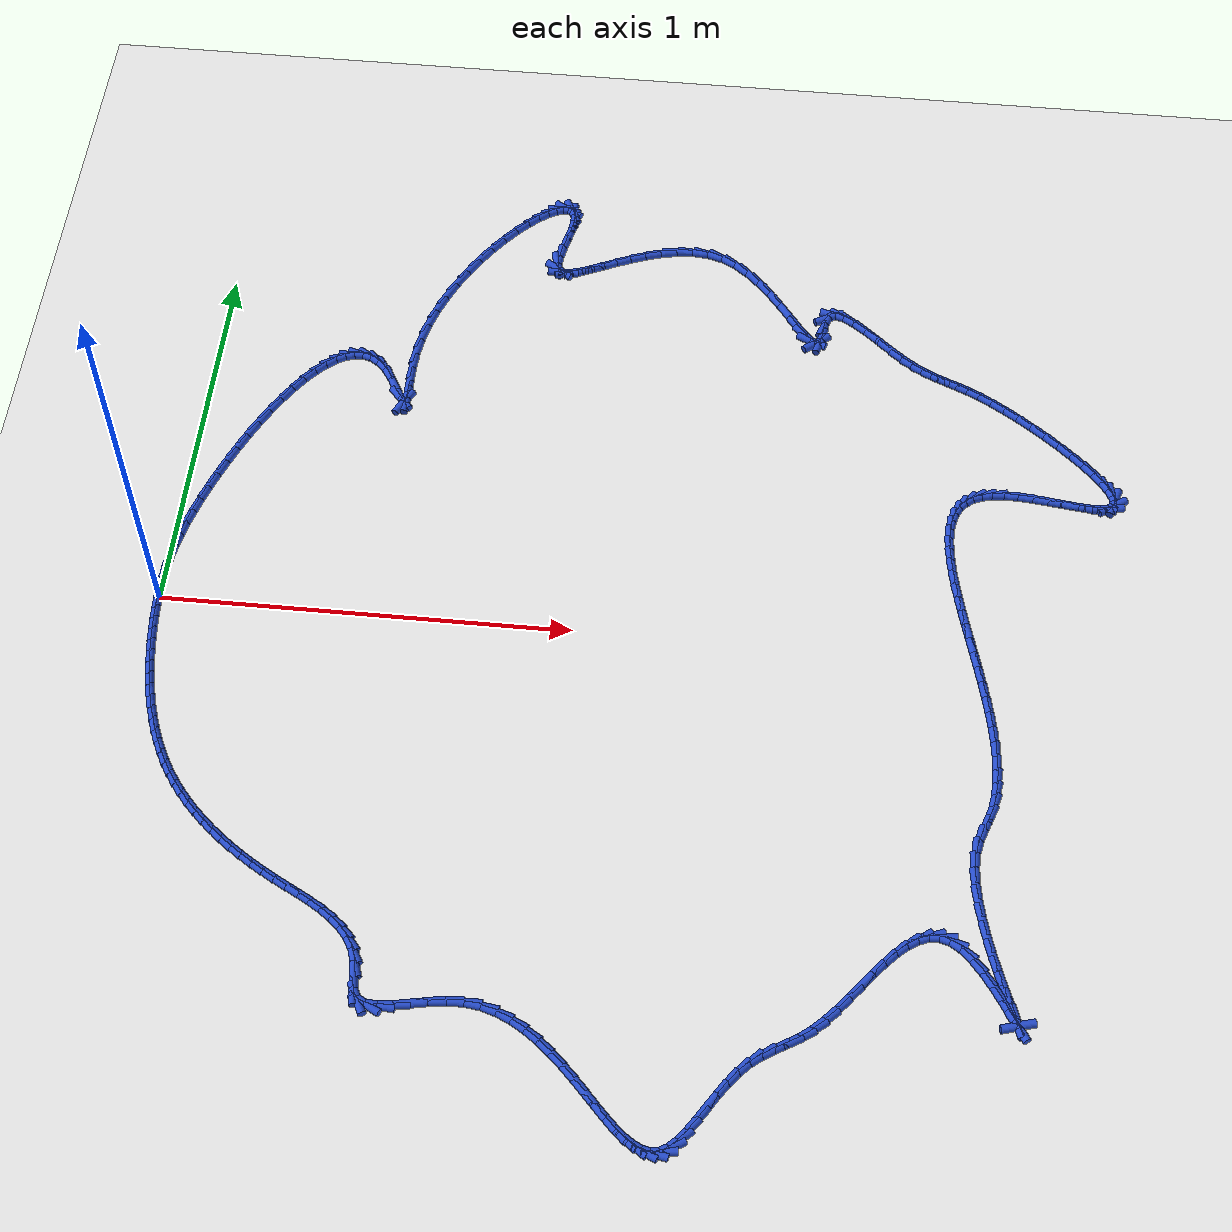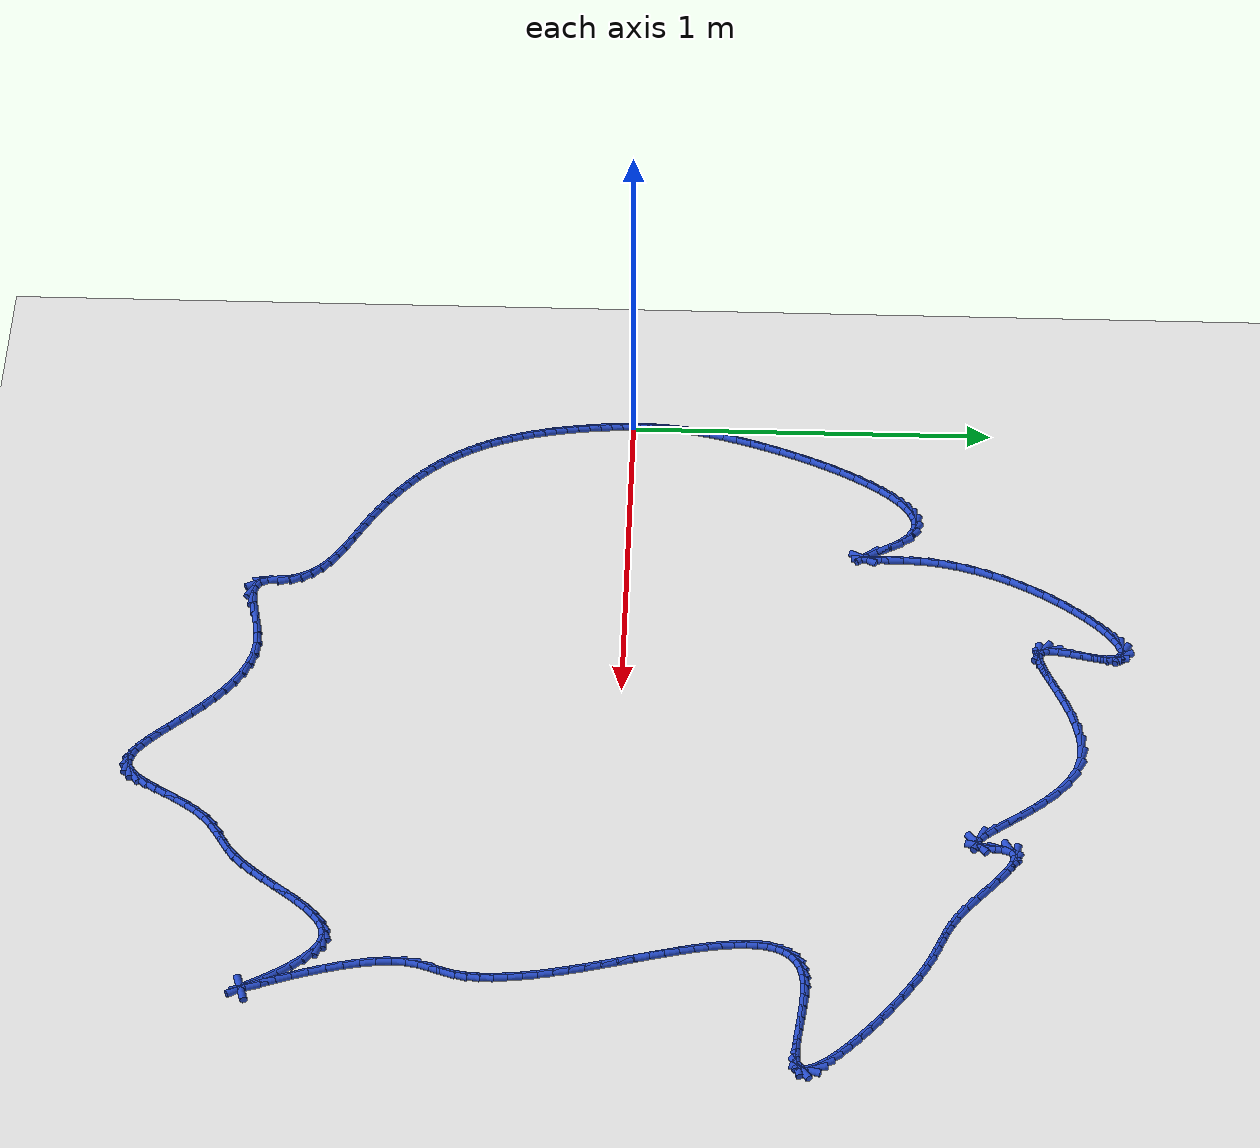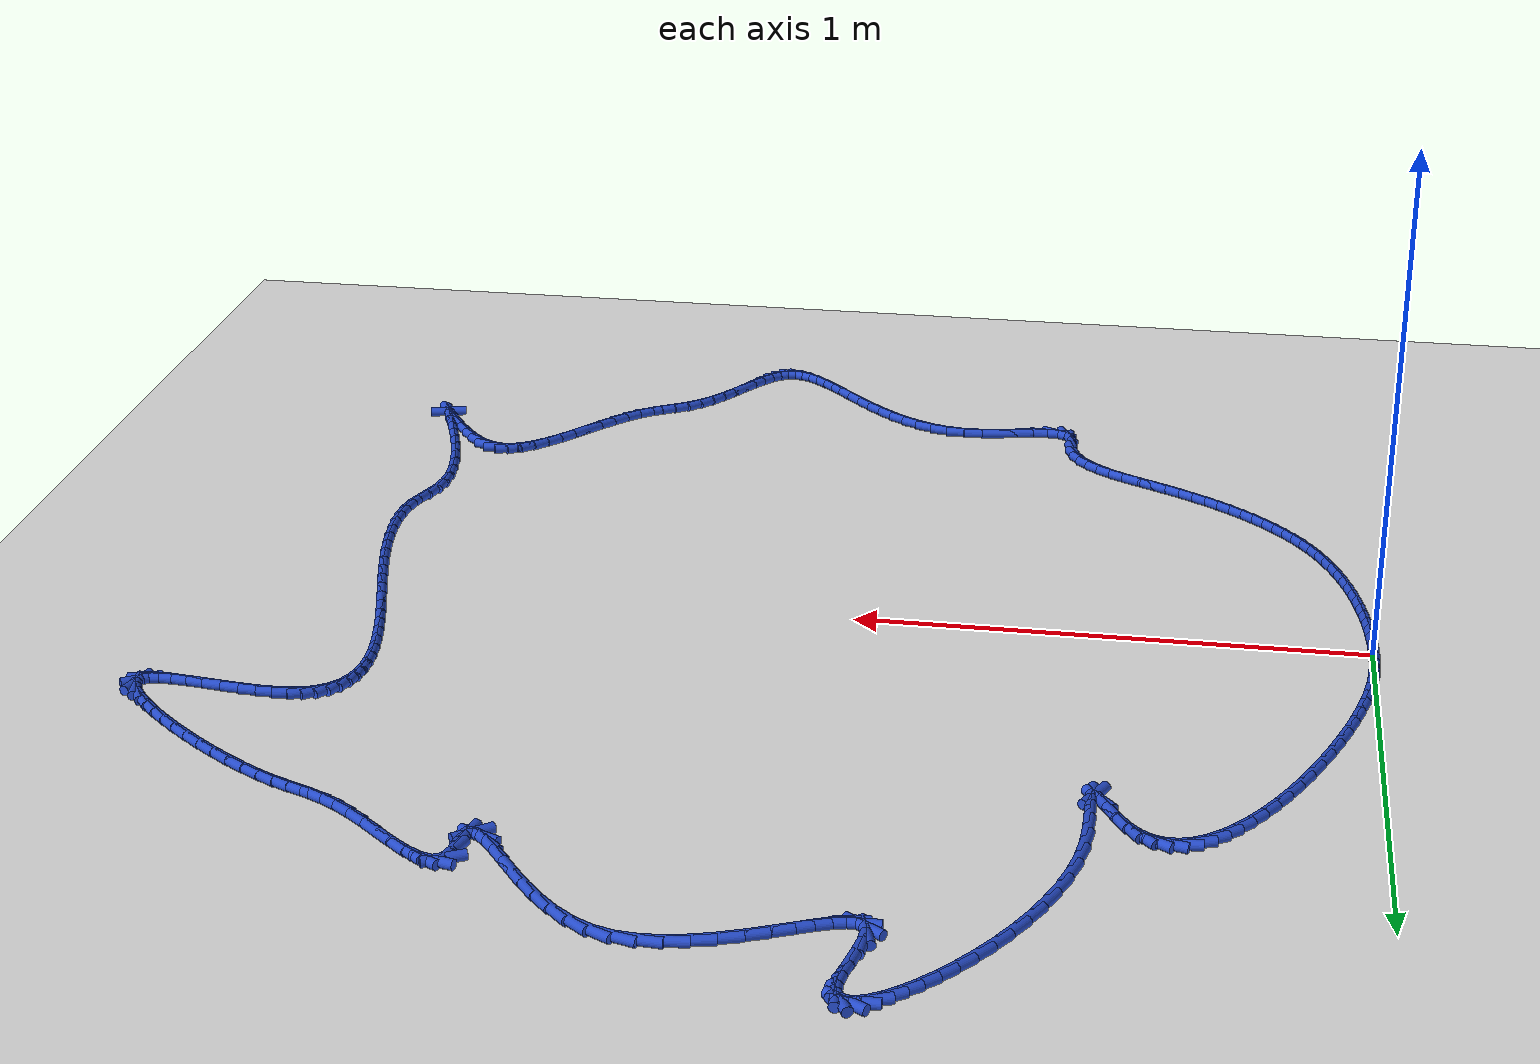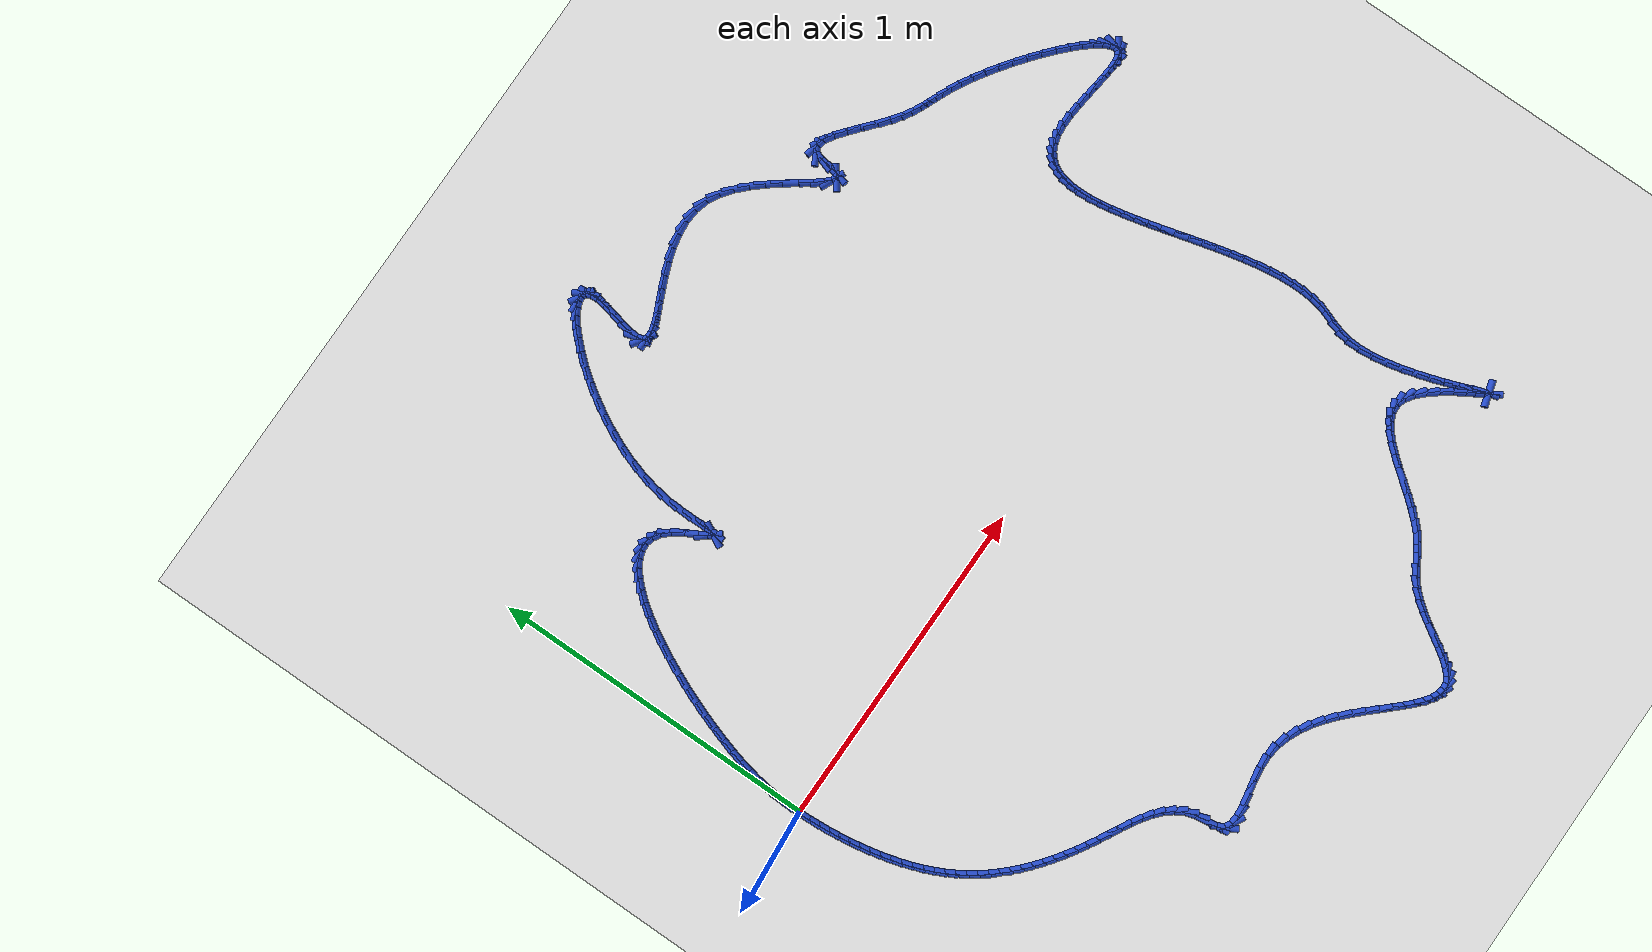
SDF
<sdf version="1.6">
 <world name="default">
  <light name="sun" type="directional">
   <pose>0 0 10 0 -0 0</pose>
   <diffuse>0.8 0.8 0.8 1</diffuse>
   <specular>0.2 0.2 0.2 1</specular>
   <attenuation>
    <range>1000</range>
    <constant>0.9</constant>
    <linear>0.01</linear>
    <quadratic>0.001</quadratic>
   </attenuation>
   <direction>-0.5 0.1 -0.9</direction>
  </light>
  <model name="ground_plane">
   <static>1</static>
   <link name="link">
    <collision name="collision">
     <geometry><plane><normal>0 0 1</normal><size>100 100</size></plane></geometry>
     <surface><friction><ode><mu>100</mu><mu2>50</mu2></ode></friction></surface>
    </collision>
    <visual name="visual">
     <cast_shadows>0</cast_shadows>
     <geometry><plane><normal>0 0 1</normal><size>100 100</size></plane></geometry>
     <material>
      <script><uri>file://media/materials/scripts/gazebo.material</uri><name>Gazebo/WhiteGlow</name></script>
     </material>
    </visual>
   </link>
  </model>
  <gravity>0 0 -9.8</gravity>
  <magnetic_field>6e-06 2.3e-05 -4.2e-05</magnetic_field>
  <atmosphere type="adiabatic"/>
  <physics name="default_physics" default="0" type="ode">
   <max_step_size>0.001</max_step_size>
   <real_time_factor>1</real_time_factor>
   <real_time_update_rate>1000</real_time_update_rate>
  </physics>
  <scene><ambient>0.4 0.4 0.4 1</ambient><background>0.7 0.7 0.7 1</background><shadows>1</shadows></scene>
  <spherical_coordinates>
   <surface_model>EARTH_WGS84</surface_model>
   <latitude_deg>0</latitude_deg>
   <longitude_deg>0</longitude_deg>
   <elevation>0</elevation>
   <heading_deg>0</heading_deg>
  </spherical_coordinates>
  <model name="line">
   <link name="link_0">
    <pose>-4.119968255444917e-18 -2.0816681711721685e-17 0.01 0 1.57 -1.562052817737333</pose>
    <collision name="collision">
     <geometry><cylinder><radius>0.01</radius><length>0.08</length></cylinder></geometry>
    </collision>
    <visual name="visual">
     <material>
      <script><name>Gazebo/Blue</name><uri>file://media/materials/scripts/gazebo.material</uri></script>
     </material>
     <geometry><cylinder><radius>0.01</radius><length>0.08</length></cylinder></geometry>
    </visual>
   </link>
   <link name="link_1">
    <pose>-0.00025625882855209964 0.02930771805601609 0.01 0 1.57 1.5480821553851039</pose>
    <collision name="collision">
     <geometry><cylinder><radius>0.01</radius><length>0.08</length></cylinder></geometry>
    </collision>
    <visual name="visual">
     <material>
      <script><name>Gazebo/Blue</name><uri>file://media/materials/scripts/gazebo.material</uri></script>
     </material>
     <geometry><cylinder><radius>0.01</radius><length>0.08</length></cylinder></geometry>
    </visual>
   </link>
   <link name="link_2">
    <pose>0.0004032373809765437 0.05833729500970832 0.01 0 1.57 1.5113289155813903</pose>
    <collision name="collision">
     <geometry><cylinder><radius>0.01</radius><length>0.08</length></cylinder></geometry>
    </collision>
    <visual name="visual">
     <material>
      <script><name>Gazebo/Blue</name><uri>file://media/materials/scripts/gazebo.material</uri></script>
     </material>
     <geometry><cylinder><radius>0.01</radius><length>0.08</length></cylinder></geometry>
    </visual>
   </link>
   <link name="link_3">
    <pose>0.0021424498949278595 0.08754929242037619 0.01 0 1.57 1.4712141610465388</pose>
    <collision name="collision">
     <geometry><cylinder><radius>0.01</radius><length>0.08</length></cylinder></geometry>
    </collision>
    <visual name="visual">
     <material>
      <script><name>Gazebo/Blue</name><uri>file://media/materials/scripts/gazebo.material</uri></script>
     </material>
     <geometry><cylinder><radius>0.01</radius><length>0.08</length></cylinder></geometry>
    </visual>
   </link>
   <link name="link_4">
    <pose>0.005125339979643774 0.11740427184731916 0.01 0 1.57 1.4299160984193249</pose>
    <collision name="collision">
     <geometry><cylinder><radius>0.01</radius><length>0.08</length></cylinder></geometry>
    </collision>
    <visual name="visual">
     <material>
      <script><name>Gazebo/Blue</name><uri>file://media/materials/scripts/gazebo.material</uri></script>
     </material>
     <geometry><cylinder><radius>0.01</radius><length>0.08</length></cylinder></geometry>
    </visual>
   </link>
   <link name="link_5">
    <pose>0.009515868901466214 0.14836279484983672 0.01 0 1.57 1.389487047491639</pose>
    <collision name="collision">
     <geometry><cylinder><radius>0.01</radius><length>0.08</length></cylinder></geometry>
    </collision>
    <visual name="visual">
     <material>
      <script><name>Gazebo/Blue</name><uri>file://media/materials/scripts/gazebo.material</uri></script>
     </material>
     <geometry><cylinder><radius>0.01</radius><length>0.08</length></cylinder></geometry>
    </visual>
   </link>
   <link name="link_6">
    <pose>0.015477997926737123 0.18088542298722837 0.01 0 1.57 1.3515616071787484</pose>
    <collision name="collision">
     <geometry><cylinder><radius>0.01</radius><length>0.08</length></cylinder></geometry>
    </collision>
    <visual name="visual">
     <material>
      <script><name>Gazebo/Blue</name><uri>file://media/materials/scripts/gazebo.material</uri></script>
     </material>
     <geometry><cylinder><radius>0.01</radius><length>0.08</length></cylinder></geometry>
    </visual>
   </link>
   <link name="link_7">
    <pose>0.023175688321798418 0.21543271781879356 0.01 0 1.57 1.317251080010718</pose>
    <collision name="collision">
     <geometry><cylinder><radius>0.01</radius><length>0.08</length></cylinder></geometry>
    </collision>
    <visual name="visual">
     <material>
      <script><name>Gazebo/Blue</name><uri>file://media/materials/scripts/gazebo.material</uri></script>
     </material>
     <geometry><cylinder><radius>0.01</radius><length>0.08</length></cylinder></geometry>
    </visual>
   </link>
   <link name="link_8">
    <pose>0.03276298747996054 0.25243192385239993 0.01 0 1.57 1.2870819562664837</pose>
    <collision name="collision">
     <geometry><cylinder><radius>0.01</radius><length>0.08</length></cylinder></geometry>
    </collision>
    <visual name="visual">
     <material>
      <script><name>Gazebo/Blue</name><uri>file://media/materials/scripts/gazebo.material</uri></script>
     </material>
     <geometry><cylinder><radius>0.01</radius><length>0.08</length></cylinder></geometry>
    </visual>
   </link>
   <link name="link_9">
    <pose>0.044233916359303134 0.2917724928527456 0.01 0 1.57 1.2598700446901603</pose>
    <collision name="collision">
     <geometry><cylinder><radius>0.01</radius><length>0.08</length></cylinder></geometry>
    </collision>
    <visual name="visual">
     <material>
      <script><name>Gazebo/Blue</name><uri>file://media/materials/scripts/gazebo.material</uri></script>
     </material>
     <geometry><cylinder><radius>0.01</radius><length>0.08</length></cylinder></geometry>
    </visual>
   </link>
   <link name="link_10">
    <pose>0.05745304306028236 0.3329088309165293 0.01 0 1.57 1.2341789606033993</pose>
    <collision name="collision">
     <geometry><cylinder><radius>0.01</radius><length>0.08</length></cylinder></geometry>
    </collision>
    <visual name="visual">
     <material>
      <script><name>Gazebo/Blue</name><uri>file://media/materials/scripts/gazebo.material</uri></script>
     </material>
     <geometry><cylinder><radius>0.01</radius><length>0.08</length></cylinder></geometry>
    </visual>
   </link>
   <link name="link_11">
    <pose>0.07228122282280378 0.3752828665178775 0.01 0 1.57 1.208914437523704</pose>
    <collision name="collision">
     <geometry><cylinder><radius>0.01</radius><length>0.08</length></cylinder></geometry>
    </collision>
    <visual name="visual">
     <material>
      <script><name>Gazebo/Blue</name><uri>file://media/materials/scripts/gazebo.material</uri></script>
     </material>
     <geometry><cylinder><radius>0.01</radius><length>0.08</length></cylinder></geometry>
    </visual>
   </link>
   <link name="link_12">
    <pose>0.08857931088677284 0.4183365281309156 0.01 0 1.57 1.1831471618995162</pose>
    <collision name="collision">
     <geometry><cylinder><radius>0.01</radius><length>0.08</length></cylinder></geometry>
    </collision>
    <visual name="visual">
     <material>
      <script><name>Gazebo/Blue</name><uri>file://media/materials/scripts/gazebo.material</uri></script>
     </material>
     <geometry><cylinder><radius>0.01</radius><length>0.08</length></cylinder></geometry>
    </visual>
   </link>
   <link name="link_13">
    <pose>0.10620816249209507 0.46151174422976954 0.01 0 1.57 1.1559867691599481</pose>
    <collision name="collision">
     <geometry><cylinder><radius>0.01</radius><length>0.08</length></cylinder></geometry>
    </collision>
    <visual name="visual">
     <material>
      <script><name>Gazebo/Blue</name><uri>file://media/materials/scripts/gazebo.material</uri></script>
     </material>
     <geometry><cylinder><radius>0.01</radius><length>0.08</length></cylinder></geometry>
    </visual>
   </link>
   <link name="link_14">
    <pose>0.12502863287867602 0.5042504432885653 0.01 0 1.57 1.1264787319771257</pose>
    <collision name="collision">
     <geometry><cylinder><radius>0.01</radius><length>0.08</length></cylinder></geometry>
    </collision>
    <visual name="visual">
     <material>
      <script><name>Gazebo/Blue</name><uri>file://media/materials/scripts/gazebo.material</uri></script>
     </material>
     <geometry><cylinder><radius>0.01</radius><length>0.08</length></cylinder></geometry>
    </visual>
   </link>
   <link name="link_15">
    <pose>0.14490157728642114 0.5459945537814286 0.01 0 1.57 1.0934982045839046</pose>
    <collision name="collision">
     <geometry><cylinder><radius>0.01</radius><length>0.08</length></cylinder></geometry>
    </collision>
    <visual name="visual">
     <material>
      <script><name>Gazebo/Blue</name><uri>file://media/materials/scripts/gazebo.material</uri></script>
     </material>
     <geometry><cylinder><radius>0.01</radius><length>0.08</length></cylinder></geometry>
    </visual>
   </link>
   <link name="link_16">
    <pose>0.16568785095523597 0.5861860041824855 0.01 0 1.57 1.0556174273168837</pose>
    <collision name="collision">
     <geometry><cylinder><radius>0.01</radius><length>0.08</length></cylinder></geometry>
    </collision>
    <visual name="visual">
     <material>
      <script><name>Gazebo/Blue</name><uri>file://media/materials/scripts/gazebo.material</uri></script>
     </material>
     <geometry><cylinder><radius>0.01</radius><length>0.08</length></cylinder></geometry>
    </visual>
   </link>
   <link name="link_17">
    <pose>0.18724830912502605 0.6242667229658616 0.01 0 1.57 1.0109176820319465</pose>
    <collision name="collision">
     <geometry><cylinder><radius>0.01</radius><length>0.08</length></cylinder></geometry>
    </collision>
    <visual name="visual">
     <material>
      <script><name>Gazebo/Blue</name><uri>file://media/materials/scripts/gazebo.material</uri></script>
     </material>
     <geometry><cylinder><radius>0.01</radius><length>0.08</length></cylinder></geometry>
    </visual>
   </link>
   <link name="link_18">
    <pose>0.2094438070356968 0.6596786386056831 0.01 0 1.57 0.9567030457038551</pose>
    <collision name="collision">
     <geometry><cylinder><radius>0.01</radius><length>0.08</length></cylinder></geometry>
    </collision>
    <visual name="visual">
     <material>
      <script><name>Gazebo/Blue</name><uri>file://media/materials/scripts/gazebo.material</uri></script>
     </material>
     <geometry><cylinder><radius>0.01</radius><length>0.08</length></cylinder></geometry>
    </visual>
   </link>
   <link name="link_19">
    <pose>0.23213519992715384 0.6918636795760756 0.01 0 1.57 0.8890512925944463</pose>
    <collision name="collision">
     <geometry><cylinder><radius>0.01</radius><length>0.08</length></cylinder></geometry>
    </collision>
    <visual name="visual">
     <material>
      <script><name>Gazebo/Blue</name><uri>file://media/materials/scripts/gazebo.material</uri></script>
     </material>
     <geometry><cylinder><radius>0.01</radius><length>0.08</length></cylinder></geometry>
    </visual>
   </link>
   <link name="link_20">
    <pose>0.2551833430393026 0.7202637743511651 0.01 0 1.57 0.8021185245611526</pose>
    <collision name="collision">
     <geometry><cylinder><radius>0.01</radius><length>0.08</length></cylinder></geometry>
    </collision>
    <visual name="visual">
     <material>
      <script><name>Gazebo/Blue</name><uri>file://media/materials/scripts/gazebo.material</uri></script>
     </material>
     <geometry><cylinder><radius>0.01</radius><length>0.08</length></cylinder></geometry>
    </visual>
   </link>
   <link name="link_21">
    <pose>0.27844909161204867 0.7443208514050774 0.01 0 1.57 0.687169390009512</pose>
    <collision name="collision">
     <geometry><cylinder><radius>0.01</radius><length>0.08</length></cylinder></geometry>
    </collision>
    <visual name="visual">
     <material>
      <script><name>Gazebo/Blue</name><uri>file://media/materials/scripts/gazebo.material</uri></script>
     </material>
     <geometry><cylinder><radius>0.01</radius><length>0.08</length></cylinder></geometry>
    </visual>
   </link>
   <link name="link_22">
    <pose>0.3017933008852976 0.7634768392119387 0.01 0 1.57 0.5317443519429484</pose>
    <collision name="collision">
     <geometry><cylinder><radius>0.01</radius><length>0.08</length></cylinder></geometry>
    </collision>
    <visual name="visual">
     <material>
      <script><name>Gazebo/Blue</name><uri>file://media/materials/scripts/gazebo.material</uri></script>
     </material>
     <geometry><cylinder><radius>0.01</radius><length>0.08</length></cylinder></geometry>
    </visual>
   </link>
   <link name="link_23">
    <pose>0.32507682609895466 0.7771736662458741 0.01 0 1.57 0.32116675374424</pose>
    <collision name="collision">
     <geometry><cylinder><radius>0.01</radius><length>0.08</length></cylinder></geometry>
    </collision>
    <visual name="visual">
     <material>
      <script><name>Gazebo/Blue</name><uri>file://media/materials/scripts/gazebo.material</uri></script>
     </material>
     <geometry><cylinder><radius>0.01</radius><length>0.08</length></cylinder></geometry>
    </visual>
   </link>
   <link name="link_24">
    <pose>0.3481605224929256 0.7848532609810102 0.01 0 1.57 0.04851342651883742</pose>
    <collision name="collision">
     <geometry><cylinder><radius>0.01</radius><length>0.08</length></cylinder></geometry>
    </collision>
    <visual name="visual">
     <material>
      <script><name>Gazebo/Blue</name><uri>file://media/materials/scripts/gazebo.material</uri></script>
     </material>
     <geometry><cylinder><radius>0.01</radius><length>0.08</length></cylinder></geometry>
    </visual>
   </link>
   <link name="link_25">
    <pose>0.37090524530711605 0.785957551891473 0.01 0 1.57 -0.2644275330406125</pose>
    <collision name="collision">
     <geometry><cylinder><radius>0.01</radius><length>0.08</length></cylinder></geometry>
    </collision>
    <visual name="visual">
     <material>
      <script><name>Gazebo/Blue</name><uri>file://media/materials/scripts/gazebo.material</uri></script>
     </material>
     <geometry><cylinder><radius>0.01</radius><length>0.08</length></cylinder></geometry>
    </visual>
   </link>
   <link name="link_26">
    <pose>0.39317184978143094 0.7799284674513873 0.01 0 1.57 -0.5648753291209293</pose>
    <collision name="collision">
     <geometry><cylinder><radius>0.01</radius><length>0.08</length></cylinder></geometry>
    </collision>
    <visual name="visual">
     <material>
      <script><name>Gazebo/Blue</name><uri>file://media/materials/scripts/gazebo.material</uri></script>
     </material>
     <geometry><cylinder><radius>0.01</radius><length>0.08</length></cylinder></geometry>
    </visual>
   </link>
   <link name="link_27">
    <pose>0.4148211911557764 0.7662079361348799 0.01 0 1.57 -0.8105221627786867</pose>
    <collision name="collision">
     <geometry><cylinder><radius>0.01</radius><length>0.08</length></cylinder></geometry>
    </collision>
    <visual name="visual">
     <material>
      <script><name>Gazebo/Blue</name><uri>file://media/materials/scripts/gazebo.material</uri></script>
     </material>
     <geometry><cylinder><radius>0.01</radius><length>0.08</length></cylinder></geometry>
    </visual>
   </link>
   <link name="link_28">
    <pose>0.43571412467005766 0.7442378864160764 0.01 0 1.57 -0.9883571259702624</pose>
    <collision name="collision">
     <geometry><cylinder><radius>0.01</radius><length>0.08</length></cylinder></geometry>
    </collision>
    <visual name="visual">
     <material>
      <script><name>Gazebo/Blue</name><uri>file://media/materials/scripts/gazebo.material</uri></script>
     </material>
     <geometry><cylinder><radius>0.01</radius><length>0.08</length></cylinder></geometry>
    </visual>
   </link>
   <link name="link_29">
    <pose>0.4556354778369066 0.7139926225326337 0.01 0 1.57 -1.0718815724279143</pose>
    <collision name="collision">
     <geometry><cylinder><radius>0.01</radius><length>0.08</length></cylinder></geometry>
    </collision>
    <visual name="visual">
     <material>
      <script><name>Gazebo/Blue</name><uri>file://media/materials/scripts/gazebo.material</uri></script>
     </material>
     <geometry><cylinder><radius>0.01</radius><length>0.08</length></cylinder></geometry>
    </visual>
   </link>
   <link name="link_30">
    <pose>0.4735642048301116 0.6810894877746496 0.01 0 1.57 -1.0729017904365235</pose>
    <collision name="collision">
     <geometry><cylinder><radius>0.01</radius><length>0.08</length></cylinder></geometry>
    </collision>
    <visual name="visual">
     <material>
      <script><name>Gazebo/Blue</name><uri>file://media/materials/scripts/gazebo.material</uri></script>
     </material>
     <geometry><cylinder><radius>0.01</radius><length>0.08</length></cylinder></geometry>
    </visual>
   </link>
   <link name="link_31">
    <pose>0.48799411048581626 0.6545430300878968 0.01 0 1.57 -0.8707929391712592</pose>
    <collision name="collision">
     <geometry><cylinder><radius>0.01</radius><length>0.08</length></cylinder></geometry>
    </collision>
    <visual name="visual">
     <material>
      <script><name>Gazebo/Blue</name><uri>file://media/materials/scripts/gazebo.material</uri></script>
     </material>
     <geometry><cylinder><radius>0.01</radius><length>0.08</length></cylinder></geometry>
    </visual>
   </link>
   <link name="link_32">
    <pose>0.4974334274465043 0.6433363551747635 0.01 0 1.57 1.0992074477734581</pose>
    <collision name="collision">
     <geometry><cylinder><radius>0.01</radius><length>0.08</length></cylinder></geometry>
    </collision>
    <visual name="visual">
     <material>
      <script><name>Gazebo/Blue</name><uri>file://media/materials/scripts/gazebo.material</uri></script>
     </material>
     <geometry><cylinder><radius>0.01</radius><length>0.08</length></cylinder></geometry>
    </visual>
   </link>
   <link name="link_33">
    <pose>0.5016825819778292 0.651668580165561 0.01 0 1.57 1.5351149611878014</pose>
    <collision name="collision">
     <geometry><cylinder><radius>0.01</radius><length>0.08</length></cylinder></geometry>
    </collision>
    <visual name="visual">
     <material>
      <script><name>Gazebo/Blue</name><uri>file://media/materials/scripts/gazebo.material</uri></script>
     </material>
     <geometry><cylinder><radius>0.01</radius><length>0.08</length></cylinder></geometry>
    </visual>
   </link>
   <link name="link_34">
    <pose>0.5025606061098845 0.6762654940952952 0.01 0 1.57 -1.5572992215891486</pose>
    <collision name="collision">
     <geometry><cylinder><radius>0.01</radius><length>0.08</length></cylinder></geometry>
    </collision>
    <visual name="visual">
     <material>
      <script><name>Gazebo/Blue</name><uri>file://media/materials/scripts/gazebo.material</uri></script>
     </material>
     <geometry><cylinder><radius>0.01</radius><length>0.08</length></cylinder></geometry>
    </visual>
   </link>
   <link name="link_35">
    <pose>0.5020620240711536 0.7132031747973943 0.01 0 1.57 1.5681651506826115</pose>
    <collision name="collision">
     <geometry><cylinder><radius>0.01</radius><length>0.08</length></cylinder></geometry>
    </collision>
    <visual name="visual">
     <material>
      <script><name>Gazebo/Blue</name><uri>file://media/materials/scripts/gazebo.material</uri></script>
     </material>
     <geometry><cylinder><radius>0.01</radius><length>0.08</length></cylinder></geometry>
    </visual>
   </link>
   <link name="link_36">
    <pose>0.5021813600901192 0.7585577001052859 0.01 0 1.57 1.5160483201674366</pose>
    <collision name="collision">
     <geometry><cylinder><radius>0.01</radius><length>0.08</length></cylinder></geometry>
    </collision>
    <visual name="visual">
     <material>
      <script><name>Gazebo/Blue</name><uri>file://media/materials/scripts/gazebo.material</uri></script>
     </material>
     <geometry><cylinder><radius>0.01</radius><length>0.08</length></cylinder></geometry>
    </visual>
   </link>
   <link name="link_37">
    <pose>0.5049131383952644 0.8084051478523981 0.01 0 1.57 1.432313511323994</pose>
    <collision name="collision">
     <geometry><cylinder><radius>0.01</radius><length>0.08</length></cylinder></geometry>
    </collision>
    <visual name="visual">
     <material>
      <script><name>Gazebo/Blue</name><uri>file://media/materials/scripts/gazebo.material</uri></script>
     </material>
     <geometry><cylinder><radius>0.01</radius><length>0.08</length></cylinder></geometry>
    </visual>
   </link>
   <link name="link_38">
    <pose>0.5119899636487898 0.8591806083599576 0.01 0 1.57 1.3463404895163555</pose>
    <collision name="collision">
     <geometry><cylinder><radius>0.01</radius><length>0.08</length></cylinder></geometry>
    </collision>
    <visual name="visual">
     <material>
      <script><name>Gazebo/Blue</name><uri>file://media/materials/scripts/gazebo.material</uri></script>
     </material>
     <geometry><cylinder><radius>0.01</radius><length>0.08</length></cylinder></geometry>
    </visual>
   </link>
   <link name="link_39">
    <pose>0.5234959880895468 0.9095787015212802 0.01 0 1.57 1.270078652641686</pose>
    <collision name="collision">
     <geometry><cylinder><radius>0.01</radius><length>0.08</length></cylinder></geometry>
    </collision>
    <visual name="visual">
     <material>
      <script><name>Gazebo/Blue</name><uri>file://media/materials/scripts/gazebo.material</uri></script>
     </material>
     <geometry><cylinder><radius>0.01</radius><length>0.08</length></cylinder></geometry>
    </visual>
   </link>
   <link name="link_40">
    <pose>0.5388756560525543 0.9591708932373276 0.01 0 1.57 1.201886004252048</pose>
    <collision name="collision">
     <geometry><cylinder><radius>0.01</radius><length>0.08</length></cylinder></geometry>
    </collision>
    <visual name="visual">
     <material>
      <script><name>Gazebo/Blue</name><uri>file://media/materials/scripts/gazebo.material</uri></script>
     </material>
     <geometry><cylinder><radius>0.01</radius><length>0.08</length></cylinder></geometry>
    </visual>
   </link>
   <link name="link_41">
    <pose>0.5575720002904395 1.0075305842614835 0.01 0 1.57 1.1401210553718055</pose>
    <collision name="collision">
     <geometry><cylinder><radius>0.01</radius><length>0.08</length></cylinder></geometry>
    </collision>
    <visual name="visual">
     <material>
      <script><name>Gazebo/Blue</name><uri>file://media/materials/scripts/gazebo.material</uri></script>
     </material>
     <geometry><cylinder><radius>0.01</radius><length>0.08</length></cylinder></geometry>
    </visual>
   </link>
   <link name="link_42">
    <pose>0.5790280535558285 1.054231175347129 0.01 0 1.57 1.0832120006053216</pose>
    <collision name="collision">
     <geometry><cylinder><radius>0.01</radius><length>0.08</length></cylinder></geometry>
    </collision>
    <visual name="visual">
     <material>
      <script><name>Gazebo/Blue</name><uri>file://media/materials/scripts/gazebo.material</uri></script>
     </material>
     <geometry><cylinder><radius>0.01</radius><length>0.08</length></cylinder></geometry>
    </visual>
   </link>
   <link name="link_43">
    <pose>0.6026868486013476 1.0988460672476459 0.01 0 1.57 1.0296259626467044</pose>
    <collision name="collision">
     <geometry><cylinder><radius>0.01</radius><length>0.08</length></cylinder></geometry>
    </collision>
    <visual name="visual">
     <material>
      <script><name>Gazebo/Blue</name><uri>file://media/materials/scripts/gazebo.material</uri></script>
     </material>
     <geometry><cylinder><radius>0.01</radius><length>0.08</length></cylinder></geometry>
    </visual>
   </link>
   <link name="link_44">
    <pose>0.6279914181796239 1.1409486607164168 0.01 0 1.57 0.9777858380400524</pose>
    <collision name="collision">
     <geometry><cylinder><radius>0.01</radius><length>0.08</length></cylinder></geometry>
    </collision>
    <visual name="visual">
     <material>
      <script><name>Gazebo/Blue</name><uri>file://media/materials/scripts/gazebo.material</uri></script>
     </material>
     <geometry><cylinder><radius>0.01</radius><length>0.08</length></cylinder></geometry>
    </visual>
   </link>
   <link name="link_45">
    <pose>0.6543847950432836 1.1801123565068234 0.01 0 1.57 0.9259277449278839</pose>
    <collision name="collision">
     <geometry><cylinder><radius>0.01</radius><length>0.08</length></cylinder></geometry>
    </collision>
    <visual name="visual">
     <material>
      <script><name>Gazebo/Blue</name><uri>file://media/materials/scripts/gazebo.material</uri></script>
     </material>
     <geometry><cylinder><radius>0.01</radius><length>0.08</length></cylinder></geometry>
    </visual>
   </link>
   <link name="link_46">
    <pose>0.6813100119449528 1.2159105553722473 0.01 0 1.57 0.8718624575269105</pose>
    <collision name="collision">
     <geometry><cylinder><radius>0.01</radius><length>0.08</length></cylinder></geometry>
    </collision>
    <visual name="visual">
     <material>
      <script><name>Gazebo/Blue</name><uri>file://media/materials/scripts/gazebo.material</uri></script>
     </material>
     <geometry><cylinder><radius>0.01</radius><length>0.08</length></cylinder></geometry>
    </visual>
   </link>
   <link name="link_47">
    <pose>0.7082101016372588 1.2479166580660719 0.01 0 1.57 0.8125498130418877</pose>
    <collision name="collision">
     <geometry><cylinder><radius>0.01</radius><length>0.08</length></cylinder></geometry>
    </collision>
    <visual name="visual">
     <material>
      <script><name>Gazebo/Blue</name><uri>file://media/materials/scripts/gazebo.material</uri></script>
     </material>
     <geometry><cylinder><radius>0.01</radius><length>0.08</length></cylinder></geometry>
    </visual>
   </link>
   <link name="link_48">
    <pose>0.7345280968728276 1.275704065341678 0.01 0 1.57 0.7432712633868042</pose>
    <collision name="collision">
     <geometry><cylinder><radius>0.01</radius><length>0.08</length></cylinder></geometry>
    </collision>
    <visual name="visual">
     <material>
      <script><name>Gazebo/Blue</name><uri>file://media/materials/scripts/gazebo.material</uri></script>
     </material>
     <geometry><cylinder><radius>0.01</radius><length>0.08</length></cylinder></geometry>
    </visual>
   </link>
   <link name="link_49">
    <pose>0.759707030404286 1.2988461779524478 0.01 0 1.57 0.6558680557648784</pose>
    <collision name="collision">
     <geometry><cylinder><radius>0.01</radius><length>0.08</length></cylinder></geometry>
    </collision>
    <visual name="visual">
     <material>
      <script><name>Gazebo/Blue</name><uri>file://media/materials/scripts/gazebo.material</uri></script>
     </material>
     <geometry><cylinder><radius>0.01</radius><length>0.08</length></cylinder></geometry>
    </visual>
   </link>
   <link name="link_50">
    <pose>0.78318993498426 1.3169163966517636 0.01 0 1.57 0.5346426273832897</pose>
    <collision name="collision">
     <geometry><cylinder><radius>0.01</radius><length>0.08</length></cylinder></geometry>
    </collision>
    <visual name="visual">
     <material>
      <script><name>Gazebo/Blue</name><uri>file://media/materials/scripts/gazebo.material</uri></script>
     </material>
     <geometry><cylinder><radius>0.01</radius><length>0.08</length></cylinder></geometry>
    </visual>
   </link>
   <link name="link_51">
    <pose>0.8044198433653768 1.3294881221930075 0.01 0 1.57 0.3462980567022738</pose>
    <collision name="collision">
     <geometry><cylinder><radius>0.01</radius><length>0.08</length></cylinder></geometry>
    </collision>
    <visual name="visual">
     <material>
      <script><name>Gazebo/Blue</name><uri>file://media/materials/scripts/gazebo.material</uri></script>
     </material>
     <geometry><cylinder><radius>0.01</radius><length>0.08</length></cylinder></geometry>
    </visual>
   </link>
   <link name="link_52">
    <pose>0.8228397883002623 1.336134755329561 0.01 0 1.57 0.01959100987693563</pose>
    <collision name="collision">
     <geometry><cylinder><radius>0.01</radius><length>0.08</length></cylinder></geometry>
    </collision>
    <visual name="visual">
     <material>
      <script><name>Gazebo/Blue</name><uri>file://media/materials/scripts/gazebo.material</uri></script>
     </material>
     <geometry><cylinder><radius>0.01</radius><length>0.08</length></cylinder></geometry>
    </visual>
   </link>
   <link name="link_53">
    <pose>0.8378928025415433 1.3364296968148064 0.01 0 1.57 -0.5274953421119011</pose>
    <collision name="collision">
     <geometry><cylinder><radius>0.01</radius><length>0.08</length></cylinder></geometry>
    </collision>
    <visual name="visual">
     <material>
      <script><name>Gazebo/Blue</name><uri>file://media/materials/scripts/gazebo.material</uri></script>
     </material>
     <geometry><cylinder><radius>0.01</radius><length>0.08</length></cylinder></geometry>
    </visual>
   </link>
   <link name="link_54">
    <pose>0.8490219188418462 1.329946347402126 0.01 0 1.57 -1.11866152106982</pose>
    <collision name="collision">
     <geometry><cylinder><radius>0.01</radius><length>0.08</length></cylinder></geometry>
    </collision>
    <visual name="visual">
     <material>
      <script><name>Gazebo/Blue</name><uri>file://media/materials/scripts/gazebo.material</uri></script>
     </material>
     <geometry><cylinder><radius>0.01</radius><length>0.08</length></cylinder></geometry>
    </visual>
   </link>
   <link name="link_55">
    <pose>0.8556701699537981 1.3162581078449018 0.01 0 1.57 -1.4954029561490114</pose>
    <collision name="collision">
     <geometry><cylinder><radius>0.01</radius><length>0.08</length></cylinder></geometry>
    </collision>
    <visual name="visual">
     <material>
      <script><name>Gazebo/Blue</name><uri>file://media/materials/scripts/gazebo.material</uri></script>
     </material>
     <geometry><cylinder><radius>0.01</radius><length>0.08</length></cylinder></geometry>
    </visual>
   </link>
   <link name="link_56">
    <pose>0.8572805886300243 1.2949383788965152 0.01 0 1.57 1.4472860149760578</pose>
    <collision name="collision">
     <geometry><cylinder><radius>0.01</radius><length>0.08</length></cylinder></geometry>
    </collision>
    <visual name="visual">
     <material>
      <script><name>Gazebo/Blue</name><uri>file://media/materials/scripts/gazebo.material</uri></script>
     </material>
     <geometry><cylinder><radius>0.01</radius><length>0.08</length></cylinder></geometry>
    </visual>
   </link>
   <link name="link_57">
    <pose>0.853699308425175 1.2660901715049848 0.01 0 1.57 1.36878192493172</pose>
    <collision name="collision">
     <geometry><cylinder><radius>0.01</radius><length>0.08</length></cylinder></geometry>
    </collision>
    <visual name="visual">
     <material>
      <script><name>Gazebo/Blue</name><uri>file://media/materials/scripts/gazebo.material</uri></script>
     </material>
     <geometry><cylinder><radius>0.01</radius><length>0.08</length></cylinder></geometry>
    </visual>
   </link>
   <link name="link_58">
    <pose>0.8468215444637746 1.2325086631523583 0.01 0 1.57 1.3541646240603578</pose>
    <collision name="collision">
     <geometry><cylinder><radius>0.01</radius><length>0.08</length></cylinder></geometry>
    </collision>
    <visual name="visual">
     <material>
      <script><name>Gazebo/Blue</name><uri>file://media/materials/scripts/gazebo.material</uri></script>
     </material>
     <geometry><cylinder><radius>0.01</radius><length>0.08</length></cylinder></geometry>
    </visual>
   </link>
   <link name="link_59">
    <pose>0.8391919976442083 1.1978423520915233 0.01 0 1.57 1.3909551552863428</pose>
    <collision name="collision">
     <geometry><cylinder><radius>0.01</radius><length>0.08</length></cylinder></geometry>
    </collision>
    <visual name="visual">
     <material>
      <script><name>Gazebo/Blue</name><uri>file://media/materials/scripts/gazebo.material</uri></script>
     </material>
     <geometry><cylinder><radius>0.01</radius><length>0.08</length></cylinder></geometry>
    </visual>
   </link>
   <link name="link_60">
    <pose>0.8333556295895955 1.1657400791261041 0.01 0 1.57 1.512990473687629</pose>
    <collision name="collision">
     <geometry><cylinder><radius>0.01</radius><length>0.08</length></cylinder></geometry>
    </collision>
    <visual name="visual">
     <material>
      <script><name>Gazebo/Blue</name><uri>file://media/materials/scripts/gazebo.material</uri></script>
     </material>
     <geometry><cylinder><radius>0.01</radius><length>0.08</length></cylinder></geometry>
    </visual>
   </link>
   <link name="link_61">
    <pose>0.8318574019230558 1.1398506850597259 0.01 0 1.57 -1.2786434181935535</pose>
    <collision name="collision">
     <geometry><cylinder><radius>0.01</radius><length>0.08</length></cylinder></geometry>
    </collision>
    <visual name="visual">
     <material>
      <script><name>Gazebo/Blue</name><uri>file://media/materials/scripts/gazebo.material</uri></script>
     </material>
     <geometry><cylinder><radius>0.01</radius><length>0.08</length></cylinder></geometry>
    </visual>
   </link>
   <link name="link_62">
    <pose>0.8368602881402679 1.1232164779439235 0.01 0 1.57 -0.5853457247802646</pose>
    <collision name="collision">
     <geometry><cylinder><radius>0.01</radius><length>0.08</length></cylinder></geometry>
    </collision>
    <visual name="visual">
     <material>
      <script><name>Gazebo/Blue</name><uri>file://media/materials/scripts/gazebo.material</uri></script>
     </material>
     <geometry><cylinder><radius>0.01</radius><length>0.08</length></cylinder></geometry>
    </visual>
   </link>
   <link name="link_63">
    <pose>0.8484291077323959 1.1155482509708774 0.01 0 1.57 -0.00739623432070604</pose>
    <collision name="collision">
     <geometry><cylinder><radius>0.01</radius><length>0.08</length></cylinder></geometry>
    </collision>
    <visual name="visual">
     <material>
      <script><name>Gazebo/Blue</name><uri>file://media/materials/scripts/gazebo.material</uri></script>
     </material>
     <geometry><cylinder><radius>0.01</radius><length>0.08</length></cylinder></geometry>
    </visual>
   </link>
   <link name="link_64">
    <pose>0.865912069607281 1.1154189405302772 0.01 0 1.57 0.25716398750181846</pose>
    <collision name="collision">
     <geometry><cylinder><radius>0.01</radius><length>0.08</length></cylinder></geometry>
    </collision>
    <visual name="visual">
     <material>
      <script><name>Gazebo/Blue</name><uri>file://media/materials/scripts/gazebo.material</uri></script>
     </material>
     <geometry><cylinder><radius>0.01</radius><length>0.08</length></cylinder></geometry>
    </visual>
   </link>
   <link name="link_65">
    <pose>0.8886567650420863 1.1214005023184133 0.01 0 1.57 0.371739354481343</pose>
    <collision name="collision">
     <geometry><cylinder><radius>0.01</radius><length>0.08</length></cylinder></geometry>
    </collision>
    <visual name="visual">
     <material>
      <script><name>Gazebo/Blue</name><uri>file://media/materials/scripts/gazebo.material</uri></script>
     </material>
     <geometry><cylinder><radius>0.01</radius><length>0.08</length></cylinder></geometry>
    </visual>
   </link>
   <link name="link_66">
    <pose>0.9160107853139746 1.132064892031576 0.01 0 1.57 0.4183097120679799</pose>
    <collision name="collision">
     <geometry><cylinder><radius>0.01</radius><length>0.08</length></cylinder></geometry>
    </collision>
    <visual name="visual">
     <material>
      <script><name>Gazebo/Blue</name><uri>file://media/materials/scripts/gazebo.material</uri></script>
     </material>
     <geometry><cylinder><radius>0.01</radius><length>0.08</length></cylinder></geometry>
    </visual>
   </link>
   <link name="link_67">
    <pose>0.9473217217001088 1.1459840653660551 0.01 0 1.57 0.4269056660025699</pose>
    <collision name="collision">
     <geometry><cylinder><radius>0.01</radius><length>0.08</length></cylinder></geometry>
    </collision>
    <visual name="visual">
     <material>
      <script><name>Gazebo/Blue</name><uri>file://media/materials/scripts/gazebo.material</uri></script>
     </material>
     <geometry><cylinder><radius>0.01</radius><length>0.08</length></cylinder></geometry>
    </visual>
   </link>
   <link name="link_68">
    <pose>0.9819371654776529 1.1617299780181425 0.01 0 1.57 0.40880253399688626</pose>
    <collision name="collision">
     <geometry><cylinder><radius>0.01</radius><length>0.08</length></cylinder></geometry>
    </collision>
    <visual name="visual">
     <material>
      <script><name>Gazebo/Blue</name><uri>file://media/materials/scripts/gazebo.material</uri></script>
     </material>
     <geometry><cylinder><radius>0.01</radius><length>0.08</length></cylinder></geometry>
    </visual>
   </link>
   <link name="link_69">
    <pose>1.0192047079237687 1.1778745856841268 0.01 0 1.57 0.36745059662043017</pose>
    <collision name="collision">
     <geometry><cylinder><radius>0.01</radius><length>0.08</length></cylinder></geometry>
    </collision>
    <visual name="visual">
     <material>
      <script><name>Gazebo/Blue</name><uri>file://media/materials/scripts/gazebo.material</uri></script>
     </material>
     <geometry><cylinder><radius>0.01</radius><length>0.08</length></cylinder></geometry>
    </visual>
   </link>
   <link name="link_70">
    <pose>1.0584719403156189 1.1929898440602997 0.01 0 1.57 0.3021181947966258</pose>
    <collision name="collision">
     <geometry><cylinder><radius>0.01</radius><length>0.08</length></cylinder></geometry>
    </collision>
    <visual name="visual">
     <material>
      <script><name>Gazebo/Blue</name><uri>file://media/materials/scripts/gazebo.material</uri></script>
     </material>
     <geometry><cylinder><radius>0.01</radius><length>0.08</length></cylinder></geometry>
    </visual>
   </link>
   <link name="link_71">
    <pose>1.0990864539303677 1.2056477088429507 0.01 0 1.57 0.20925064223080006</pose>
    <collision name="collision">
     <geometry><cylinder><radius>0.01</radius><length>0.08</length></cylinder></geometry>
    </collision>
    <visual name="visual">
     <material>
      <script><name>Gazebo/Blue</name><uri>file://media/materials/scripts/gazebo.material</uri></script>
     </material>
     <geometry><cylinder><radius>0.01</radius><length>0.08</length></cylinder></geometry>
    </visual>
   </link>
   <link name="link_72">
    <pose>1.140395840045178 1.2144201357283713 0.01 0 1.57 0.0834524029597507</pose>
    <collision name="collision">
     <geometry><cylinder><radius>0.01</radius><length>0.08</length></cylinder></geometry>
    </collision>
    <visual name="visual">
     <material>
      <script><name>Gazebo/Blue</name><uri>file://media/materials/scripts/gazebo.material</uri></script>
     </material>
     <geometry><cylinder><radius>0.01</radius><length>0.08</length></cylinder></geometry>
    </visual>
   </link>
   <link name="link_73">
    <pose>1.181747689937212 1.2178790804128508 0.01 0 1.57 -0.08039649464325481</pose>
    <collision name="collision">
     <geometry><cylinder><radius>0.01</radius><length>0.08</length></cylinder></geometry>
    </collision>
    <visual name="visual">
     <material>
      <script><name>Gazebo/Blue</name><uri>file://media/materials/scripts/gazebo.material</uri></script>
     </material>
     <geometry><cylinder><radius>0.01</radius><length>0.08</length></cylinder></geometry>
    </visual>
   </link>
   <link name="link_74">
    <pose>1.2224895948836327 1.2145964985926798 0.01 0 1.57 -0.2823294477277827</pose>
    <collision name="collision">
     <geometry><cylinder><radius>0.01</radius><length>0.08</length></cylinder></geometry>
    </collision>
    <visual name="visual">
     <material>
      <script><name>Gazebo/Blue</name><uri>file://media/materials/scripts/gazebo.material</uri></script>
     </material>
     <geometry><cylinder><radius>0.01</radius><length>0.08</length></cylinder></geometry>
    </visual>
   </link>
   <link name="link_75">
    <pose>1.2619691461625315 1.2031443459711963 0.01 0 1.57 -0.4972699372786359</pose>
    <collision name="collision">
     <geometry><cylinder><radius>0.01</radius><length>0.08</length></cylinder></geometry>
    </collision>
    <visual name="visual">
     <material>
      <script><name>Gazebo/Blue</name><uri>file://media/materials/scripts/gazebo.material</uri></script>
     </material>
     <geometry><cylinder><radius>0.01</radius><length>0.08</length></cylinder></geometry>
    </visual>
   </link>
   <link name="link_76">
    <pose>1.2996151643615195 1.1827114832084356 0.01 0 1.57 -0.6630169629303563</pose>
    <collision name="collision">
     <geometry><cylinder><radius>0.01</radius><length>0.08</length></cylinder></geometry>
    </collision>
    <visual name="visual">
     <material>
      <script><name>Gazebo/Blue</name><uri>file://media/materials/scripts/gazebo.material</uri></script>
     </material>
     <geometry><cylinder><radius>0.01</radius><length>0.08</length></cylinder></geometry>
    </visual>
   </link>
   <link name="link_77">
    <pose>1.3351791944842528 1.1549377371622744 0.01 0 1.57 -0.7786359830704839</pose>
    <collision name="collision">
     <geometry><cylinder><radius>0.01</radius><length>0.08</length></cylinder></geometry>
    </collision>
    <visual name="visual">
     <material>
      <script><name>Gazebo/Blue</name><uri>file://media/materials/scripts/gazebo.material</uri></script>
     </material>
     <geometry><cylinder><radius>0.01</radius><length>0.08</length></cylinder></geometry>
    </visual>
   </link>
   <link name="link_78">
    <pose>1.3684929181276138 1.1220715408927828 0.01 0 1.57 -0.8575658672298722</pose>
    <collision name="collision">
     <geometry><cylinder><radius>0.01</radius><length>0.08</length></cylinder></geometry>
    </collision>
    <visual name="visual">
     <material>
      <script><name>Gazebo/Blue</name><uri>file://media/materials/scripts/gazebo.material</uri></script>
     </material>
     <geometry><cylinder><radius>0.01</radius><length>0.08</length></cylinder></geometry>
    </visual>
   </link>
   <link name="link_79">
    <pose>1.3993880168884854 1.0863613274600323 0.01 0 1.57 -0.9085475853623997</pose>
    <collision name="collision">
     <geometry><cylinder><radius>0.01</radius><length>0.08</length></cylinder></geometry>
    </collision>
    <visual name="visual">
     <material>
      <script><name>Gazebo/Blue</name><uri>file://media/materials/scripts/gazebo.material</uri></script>
     </material>
     <geometry><cylinder><radius>0.01</radius><length>0.08</length></cylinder></geometry>
    </visual>
   </link>
   <link name="link_80">
    <pose>1.4276961723637487 1.0500555299240921 0.01 0 1.57 -0.935411668793046</pose>
    <collision name="collision">
     <geometry><cylinder><radius>0.01</radius><length>0.08</length></cylinder></geometry>
    </collision>
    <visual name="visual">
     <material>
      <script><name>Gazebo/Blue</name><uri>file://media/materials/scripts/gazebo.material</uri></script>
     </material>
     <geometry><cylinder><radius>0.01</radius><length>0.08</length></cylinder></geometry>
    </visual>
   </link>
   <link name="link_81">
    <pose>1.4532490661502875 1.0154025813450327 0.01 0 1.57 -0.9363981305107616</pose>
    <collision name="collision">
     <geometry><cylinder><radius>0.01</radius><length>0.08</length></cylinder></geometry>
    </collision>
    <visual name="visual">
     <material>
      <script><name>Gazebo/Blue</name><uri>file://media/materials/scripts/gazebo.material</uri></script>
     </material>
     <geometry><cylinder><radius>0.01</radius><length>0.08</length></cylinder></geometry>
    </visual>
   </link>
   <link name="link_82">
    <pose>1.4758783798449833 0.984650914782924 0.01 0 1.57 -0.899638248670119</pose>
    <collision name="collision">
     <geometry><cylinder><radius>0.01</radius><length>0.08</length></cylinder></geometry>
    </collision>
    <visual name="visual">
     <material>
      <script><name>Gazebo/Blue</name><uri>file://media/materials/scripts/gazebo.material</uri></script>
     </material>
     <geometry><cylinder><radius>0.01</radius><length>0.08</length></cylinder></geometry>
    </visual>
   </link>
   <link name="link_83">
    <pose>1.4954157950447189 0.9600489632978364 0.01 0 1.57 -0.7831385400786404</pose>
    <collision name="collision">
     <geometry><cylinder><radius>0.01</radius><length>0.08</length></cylinder></geometry>
    </collision>
    <visual name="visual">
     <material>
      <script><name>Gazebo/Blue</name><uri>file://media/materials/scripts/gazebo.material</uri></script>
     </material>
     <geometry><cylinder><radius>0.01</radius><length>0.08</length></cylinder></geometry>
    </visual>
   </link>
   <link name="link_84">
    <pose>1.5116929933463763 0.9438451599498405 0.01 0 1.57 -0.4082175256456219</pose>
    <collision name="collision">
     <geometry><cylinder><radius>0.01</radius><length>0.08</length></cylinder></geometry>
    </collision>
    <visual name="visual">
     <material>
      <script><name>Gazebo/Blue</name><uri>file://media/materials/scripts/gazebo.material</uri></script>
     </material>
     <geometry><cylinder><radius>0.01</radius><length>0.08</length></cylinder></geometry>
    </visual>
   </link>
   <link name="link_85">
    <pose>1.5245416563468377 0.9382879377990063 0.01 0 1.57 0.6705315272241761</pose>
    <collision name="collision">
     <geometry><cylinder><radius>0.01</radius><length>0.08</length></cylinder></geometry>
    </collision>
    <visual name="visual">
     <material>
      <script><name>Gazebo/Blue</name><uri>file://media/materials/scripts/gazebo.material</uri></script>
     </material>
     <geometry><cylinder><radius>0.01</radius><length>0.08</length></cylinder></geometry>
    </visual>
   </link>
   <link name="link_86">
    <pose>1.5337934656429852 0.945625729905404 0.01 0 1.57 1.3299591129805237</pose>
    <collision name="collision">
     <geometry><cylinder><radius>0.01</radius><length>0.08</length></cylinder></geometry>
    </collision>
    <visual name="visual">
     <material>
      <script><name>Gazebo/Blue</name><uri>file://media/materials/scripts/gazebo.material</uri></script>
     </material>
     <geometry><cylinder><radius>0.01</radius><length>0.08</length></cylinder></geometry>
    </visual>
   </link>
   <link name="link_87">
    <pose>1.5392999445771778 0.9680458600293266 0.01 0 1.57 1.4531796591207686</pose>
    <collision name="collision">
     <geometry><cylinder><radius>0.01</radius><length>0.08</length></cylinder></geometry>
    </collision>
    <visual name="visual">
     <material>
      <script><name>Gazebo/Blue</name><uri>file://media/materials/scripts/gazebo.material</uri></script>
     </material>
     <geometry><cylinder><radius>0.01</radius><length>0.08</length></cylinder></geometry>
    </visual>
   </link>
   <link name="link_88">
    <pose>1.543168728229599 1.0007872003099911 0.01 0 1.57 1.24595004408657</pose>
    <collision name="collision">
     <geometry><cylinder><radius>0.01</radius><length>0.08</length></cylinder></geometry>
    </collision>
    <visual name="visual">
     <material>
      <script><name>Gazebo/Blue</name><uri>file://media/materials/scripts/gazebo.material</uri></script>
     </material>
     <geometry><cylinder><radius>0.01</radius><length>0.08</length></cylinder></geometry>
    </visual>
   </link>
   <link name="link_89">
    <pose>1.5517025668989222 1.0261269619829403 0.01 0 1.57 0.48543429121529447</pose>
    <collision name="collision">
     <geometry><cylinder><radius>0.01</radius><length>0.08</length></cylinder></geometry>
    </collision>
    <visual name="visual">
     <material>
      <script><name>Gazebo/Blue</name><uri>file://media/materials/scripts/gazebo.material</uri></script>
     </material>
     <geometry><cylinder><radius>0.01</radius><length>0.08</length></cylinder></geometry>
    </visual>
   </link>
   <link name="link_90">
    <pose>1.568033529402283 1.0347421601739333 0.01 0 1.57 -0.23699953399336723</pose>
    <collision name="collision">
     <geometry><cylinder><radius>0.01</radius><length>0.08</length></cylinder></geometry>
    </collision>
    <visual name="visual">
     <material>
      <script><name>Gazebo/Blue</name><uri>file://media/materials/scripts/gazebo.material</uri></script>
     </material>
     <geometry><cylinder><radius>0.01</radius><length>0.08</length></cylinder></geometry>
    </visual>
   </link>
   <link name="link_91">
    <pose>1.5908924108517428 1.0292208516914794 0.01 0 1.57 -0.5310762120733694</pose>
    <collision name="collision">
     <geometry><cylinder><radius>0.01</radius><length>0.08</length></cylinder></geometry>
    </collision>
    <visual name="visual">
     <material>
      <script><name>Gazebo/Blue</name><uri>file://media/materials/scripts/gazebo.material</uri></script>
     </material>
     <geometry><cylinder><radius>0.01</radius><length>0.08</length></cylinder></geometry>
    </visual>
   </link>
   <link name="link_92">
    <pose>1.618748312006946 1.012859309317159 0.01 0 1.57 -0.6519065475690852</pose>
    <collision name="collision">
     <geometry><cylinder><radius>0.01</radius><length>0.08</length></cylinder></geometry>
    </collision>
    <visual name="visual">
     <material>
      <script><name>Gazebo/Blue</name><uri>file://media/materials/scripts/gazebo.material</uri></script>
     </material>
     <geometry><cylinder><radius>0.01</radius><length>0.08</length></cylinder></geometry>
    </visual>
   </link>
   <link name="link_93">
    <pose>1.6500703336275353 0.9889538058325529 0.01 0 1.57 -0.7024750122180493</pose>
    <collision name="collision">
     <geometry><cylinder><radius>0.01</radius><length>0.08</length></cylinder></geometry>
    </collision>
    <visual name="visual">
     <material>
      <script><name>Gazebo/Blue</name><uri>file://media/materials/scripts/gazebo.material</uri></script>
     </material>
     <geometry><cylinder><radius>0.01</radius><length>0.08</length></cylinder></geometry>
    </visual>
   </link>
   <link name="link_94">
    <pose>1.6833275764731546 0.960800614019242 0.01 0 1.57 -0.712923200212516</pose>
    <collision name="collision">
     <geometry><cylinder><radius>0.01</radius><length>0.08</length></cylinder></geometry>
    </collision>
    <visual name="visual">
     <material>
      <script><name>Gazebo/Blue</name><uri>file://media/materials/scripts/gazebo.material</uri></script>
     </material>
     <geometry><cylinder><radius>0.01</radius><length>0.08</length></cylinder></geometry>
    </visual>
   </link>
   <link name="link_95">
    <pose>1.7169891413034475 0.9316960066588065 0.01 0 1.57 -0.688305594998043</pose>
    <collision name="collision">
     <geometry><cylinder><radius>0.01</radius><length>0.08</length></cylinder></geometry>
    </collision>
    <visual name="visual">
     <material>
      <script><name>Gazebo/Blue</name><uri>file://media/materials/scripts/gazebo.material</uri></script>
     </material>
     <geometry><cylinder><radius>0.01</radius><length>0.08</length></cylinder></geometry>
    </visual>
   </link>
   <link name="link_96">
    <pose>1.7495241288780568 0.9049362565328273 0.01 0 1.57 -0.6229155264467783</pose>
    <collision name="collision">
     <geometry><cylinder><radius>0.01</radius><length>0.08</length></cylinder></geometry>
    </collision>
    <visual name="visual">
     <material>
      <script><name>Gazebo/Blue</name><uri>file://media/materials/scripts/gazebo.material</uri></script>
     </material>
     <geometry><cylinder><radius>0.01</radius><length>0.08</length></cylinder></geometry>
    </visual>
   </link>
   <link name="link_97">
    <pose>1.779666036397663 0.8832847314413479 0.01 0 1.57 -0.5423353585340827</pose>
    <collision name="collision">
     <geometry><cylinder><radius>0.01</radius><length>0.08</length></cylinder></geometry>
    </collision>
    <visual name="visual">
     <material>
      <script><name>Gazebo/Blue</name><uri>file://media/materials/scripts/gazebo.material</uri></script>
     </material>
     <geometry><cylinder><radius>0.01</radius><length>0.08</length></cylinder></geometry>
    </visual>
   </link>
   <link name="link_98">
    <pose>1.8076902078664112 0.8663971255746208 0.01 0 1.57 -0.4702617054645472</pose>
    <collision name="collision">
     <geometry><cylinder><radius>0.01</radius><length>0.08</length></cylinder></geometry>
    </collision>
    <visual name="visual">
     <material>
      <script><name>Gazebo/Blue</name><uri>file://media/materials/scripts/gazebo.material</uri></script>
     </material>
     <geometry><cylinder><radius>0.01</radius><length>0.08</length></cylinder></geometry>
    </visual>
   </link>
   <link name="link_99">
    <pose>1.8344293436915744 0.8528057518755728 0.01 0 1.57 -0.4207945067243035</pose>
    <collision name="collision">
     <geometry><cylinder><radius>0.01</radius><length>0.08</length></cylinder></geometry>
    </collision>
    <visual name="visual">
     <material>
      <script><name>Gazebo/Blue</name><uri>file://media/materials/scripts/gazebo.material</uri></script>
     </material>
     <geometry><cylinder><radius>0.01</radius><length>0.08</length></cylinder></geometry>
    </visual>
   </link>
   <link name="link_100">
    <pose>1.8607169056589288 0.8410413886885786 0.01 0 1.57 -0.4041569513931056</pose>
    <collision name="collision">
     <geometry><cylinder><radius>0.01</radius><length>0.08</length></cylinder></geometry>
    </collision>
    <visual name="visual">
     <material>
      <script><name>Gazebo/Blue</name><uri>file://media/materials/scripts/gazebo.material</uri></script>
     </material>
     <geometry><cylinder><radius>0.01</radius><length>0.08</length></cylinder></geometry>
    </visual>
   </link>
   <link name="link_101">
    <pose>1.88738635555425 0.8296348143580119 0.01 0 1.57 -0.4219543267056081</pose>
    <collision name="collision">
     <geometry><cylinder><radius>0.01</radius><length>0.08</length></cylinder></geometry>
    </collision>
    <visual name="visual">
     <material>
      <script><name>Gazebo/Blue</name><uri>file://media/materials/scripts/gazebo.material</uri></script>
     </material>
     <geometry><cylinder><radius>0.01</radius><length>0.08</length></cylinder></geometry>
    </visual>
   </link>
   <link name="link_102">
    <pose>1.9152711551633135 0.8171168072282473 0.01 0 1.57 -0.4670162688232615</pose>
    <collision name="collision">
     <geometry><cylinder><radius>0.01</radius><length>0.08</length></cylinder></geometry>
    </collision>
    <visual name="visual">
     <material>
      <script><name>Gazebo/Blue</name><uri>file://media/materials/scripts/gazebo.material</uri></script>
     </material>
     <geometry><cylinder><radius>0.01</radius><length>0.08</length></cylinder></geometry>
    </visual>
   </link>
   <link name="link_103">
    <pose>1.9451976482278608 0.8020273323898707 0.01 0 1.57 -0.5188452574538254</pose>
    <collision name="collision">
     <geometry><cylinder><radius>0.01</radius><length>0.08</length></cylinder></geometry>
    </collision>
    <visual name="visual">
     <material>
      <script><name>Gazebo/Blue</name><uri>file://media/materials/scripts/gazebo.material</uri></script>
     </material>
     <geometry><cylinder><radius>0.01</radius><length>0.08</length></cylinder></geometry>
    </visual>
   </link>
   <link name="link_104">
    <pose>1.9774441897620272 0.7836136044732954 0.01 0 1.57 -0.560619701023901</pose>
    <collision name="collision">
     <geometry><cylinder><radius>0.01</radius><length>0.08</length></cylinder></geometry>
    </collision>
    <visual name="visual">
     <material>
      <script><name>Gazebo/Blue</name><uri>file://media/materials/scripts/gazebo.material</uri></script>
     </material>
     <geometry><cylinder><radius>0.01</radius><length>0.08</length></cylinder></geometry>
    </visual>
   </link>
   <link name="link_105">
    <pose>2.0113617994955364 0.7623196828981149 0.01 0 1.57 -0.5955330810822916</pose>
    <collision name="collision">
     <geometry><cylinder><radius>0.01</radius><length>0.08</length></cylinder></geometry>
    </collision>
    <visual name="visual">
     <material>
      <script><name>Gazebo/Blue</name><uri>file://media/materials/scripts/gazebo.material</uri></script>
     </material>
     <geometry><cylinder><radius>0.01</radius><length>0.08</length></cylinder></geometry>
    </visual>
   </link>
   <link name="link_106">
    <pose>2.046211864123551 0.7387053099789419 0.01 0 1.57 -0.6267140763308037</pose>
    <collision name="collision">
     <geometry><cylinder><radius>0.01</radius><length>0.08</length></cylinder></geometry>
    </collision>
    <visual name="visual">
     <material>
      <script><name>Gazebo/Blue</name><uri>file://media/materials/scripts/gazebo.material</uri></script>
     </material>
     <geometry><cylinder><radius>0.01</radius><length>0.08</length></cylinder></geometry>
    </visual>
   </link>
   <link name="link_107">
    <pose>2.081255770341232 0.7133302280303891 0.01 0 1.57 -0.6563918643237553</pose>
    <collision name="collision">
     <geometry><cylinder><radius>0.01</radius><length>0.08</length></cylinder></geometry>
    </collision>
    <visual name="visual">
     <material>
      <script><name>Gazebo/Blue</name><uri>file://media/materials/scripts/gazebo.material</uri></script>
     </material>
     <geometry><cylinder><radius>0.01</radius><length>0.08</length></cylinder></geometry>
    </visual>
   </link>
   <link name="link_108">
    <pose>2.1157549048437416 0.6867541793670687 0.01 0 1.57 -0.6864639647730861</pose>
    <collision name="collision">
     <geometry><cylinder><radius>0.01</radius><length>0.08</length></cylinder></geometry>
    </collision>
    <visual name="visual">
     <material>
      <script><name>Gazebo/Blue</name><uri>file://media/materials/scripts/gazebo.material</uri></script>
     </material>
     <geometry><cylinder><radius>0.01</radius><length>0.08</length></cylinder></geometry>
    </visual>
   </link>
   <link name="link_109">
    <pose>2.1489706543262432 0.6595369063035934 0.01 0 1.57 -0.7189066676254009</pose>
    <collision name="collision">
     <geometry><cylinder><radius>0.01</radius><length>0.08</length></cylinder></geometry>
    </collision>
    <visual name="visual">
     <material>
      <script><name>Gazebo/Blue</name><uri>file://media/materials/scripts/gazebo.material</uri></script>
     </material>
     <geometry><cylinder><radius>0.01</radius><length>0.08</length></cylinder></geometry>
    </visual>
   </link>
   <link name="link_110">
    <pose>2.1801644054838976 0.632238151154576 0.01 0 1.57 -0.7562202286700123</pose>
    <collision name="collision">
     <geometry><cylinder><radius>0.01</radius><length>0.08</length></cylinder></geometry>
    </collision>
    <visual name="visual">
     <material>
      <script><name>Gazebo/Blue</name><uri>file://media/materials/scripts/gazebo.material</uri></script>
     </material>
     <geometry><cylinder><radius>0.01</radius><length>0.08</length></cylinder></geometry>
    </visual>
   </link>
   <link name="link_111">
    <pose>2.2085975450118664 0.6054176562346287 0.01 0 1.57 -0.8021284220906618</pose>
    <collision name="collision">
     <geometry><cylinder><radius>0.01</radius><length>0.08</length></cylinder></geometry>
    </collision>
    <visual name="visual">
     <material>
      <script><name>Gazebo/Blue</name><uri>file://media/materials/scripts/gazebo.material</uri></script>
     </material>
     <geometry><cylinder><radius>0.01</radius><length>0.08</length></cylinder></geometry>
    </visual>
   </link>
   <link name="link_112">
    <pose>2.2335314596053126 0.5796351638583643 0.01 0 1.57 -0.8629740578941674</pose>
    <collision name="collision">
     <geometry><cylinder><radius>0.01</radius><length>0.08</length></cylinder></geometry>
    </collision>
    <visual name="visual">
     <material>
      <script><name>Gazebo/Blue</name><uri>file://media/materials/scripts/gazebo.material</uri></script>
     </material>
     <geometry><cylinder><radius>0.01</radius><length>0.08</length></cylinder></geometry>
    </visual>
   </link>
   <link name="link_113">
    <pose>2.254227535959398 0.5554504163403958 0.01 0 1.57 -0.9509718096589719</pose>
    <collision name="collision">
     <geometry><cylinder><radius>0.01</radius><length>0.08</length></cylinder></geometry>
    </collision>
    <visual name="visual">
     <material>
      <script><name>Gazebo/Blue</name><uri>file://media/materials/scripts/gazebo.material</uri></script>
     </material>
     <geometry><cylinder><radius>0.01</radius><length>0.08</length></cylinder></geometry>
    </visual>
   </link>
   <link name="link_114">
    <pose>2.269947160769284 0.5334231559953346 0.01 0 1.57 -1.0927724434404391</pose>
    <collision name="collision">
     <geometry><cylinder><radius>0.01</radius><length>0.08</length></cylinder></geometry>
    </collision>
    <visual name="visual">
     <material>
      <script><name>Gazebo/Blue</name><uri>file://media/materials/scripts/gazebo.material</uri></script>
     </material>
     <geometry><cylinder><radius>0.01</radius><length>0.08</length></cylinder></geometry>
    </visual>
   </link>
   <link name="link_115">
    <pose>2.279951720730133 0.5141131251377941 0.01 0 1.57 -1.3528419273760768</pose>
    <collision name="collision">
     <geometry><cylinder><radius>0.01</radius><length>0.08</length></cylinder></geometry>
    </collision>
    <visual name="visual">
     <material>
      <script><name>Gazebo/Blue</name><uri>file://media/materials/scripts/gazebo.material</uri></script>
     </material>
     <geometry><cylinder><radius>0.01</radius><length>0.08</length></cylinder></geometry>
    </visual>
   </link>
   <link name="link_116">
    <pose>2.2835026025371077 0.49808006608238664 0.01 0 1.57 1.2806559688725072</pose>
    <collision name="collision">
     <geometry><cylinder><radius>0.01</radius><length>0.08</length></cylinder></geometry>
    </collision>
    <visual name="visual">
     <material>
      <script><name>Gazebo/Blue</name><uri>file://media/materials/scripts/gazebo.material</uri></script>
     </material>
     <geometry><cylinder><radius>0.01</radius><length>0.08</length></cylinder></geometry>
    </visual>
   </link>
   <link name="link_117">
    <pose>2.279861192885369 0.48588372114372474 0.01 0 1.57 0.5939113839688589</pose>
    <collision name="collision">
     <geometry><cylinder><radius>0.01</radius><length>0.08</length></cylinder></geometry>
    </collision>
    <visual name="visual">
     <material>
      <script><name>Gazebo/Blue</name><uri>file://media/materials/scripts/gazebo.material</uri></script>
     </material>
     <geometry><cylinder><radius>0.01</radius><length>0.08</length></cylinder></geometry>
    </visual>
   </link>
   <link name="link_118">
    <pose>2.268299195440981 0.47807665088106677 0.01 0 1.57 0.17348175496115986</pose>
    <collision name="collision">
     <geometry><cylinder><radius>0.01</radius><length>0.08</length></cylinder></geometry>
    </collision>
    <visual name="visual">
     <material>
      <script><name>Gazebo/Blue</name><uri>file://media/materials/scripts/gazebo.material</uri></script>
     </material>
     <geometry><cylinder><radius>0.01</radius><length>0.08</length></cylinder></geometry>
    </visual>
   </link>
   <link name="link_119">
    <pose>2.2488647916275686 0.47467090126400513 0.01 0 1.57 -0.003847392541179653</pose>
    <collision name="collision">
     <geometry><cylinder><radius>0.01</radius><length>0.08</length></cylinder></geometry>
    </collision>
    <visual name="visual">
     <material>
      <script><name>Gazebo/Blue</name><uri>file://media/materials/scripts/gazebo.material</uri></script>
     </material>
     <geometry><cylinder><radius>0.01</radius><length>0.08</length></cylinder></geometry>
    </visual>
   </link>
   <link name="link_120">
    <pose>2.222910206660673 0.4747707592333302 0.01 0 1.57 -0.08441396217936022</pose>
    <collision name="collision">
     <geometry><cylinder><radius>0.01</radius><length>0.08</length></cylinder></geometry>
    </collision>
    <visual name="visual">
     <material>
      <script><name>Gazebo/Blue</name><uri>file://media/materials/scripts/gazebo.material</uri></script>
     </material>
     <geometry><cylinder><radius>0.01</radius><length>0.08</length></cylinder></geometry>
    </visual>
   </link>
   <link name="link_121">
    <pose>2.1919124703637776 0.47739363388846046 0.01 0 1.57 -0.11987490327351906</pose>
    <collision name="collision">
     <geometry><cylinder><radius>0.01</radius><length>0.08</length></cylinder></geometry>
    </collision>
    <visual name="visual">
     <material>
      <script><name>Gazebo/Blue</name><uri>file://media/materials/scripts/gazebo.material</uri></script>
     </material>
     <geometry><cylinder><radius>0.01</radius><length>0.08</length></cylinder></geometry>
    </visual>
   </link>
   <link name="link_122">
    <pose>2.1573486125603667 0.48155693432881447 0.01 0 1.57 -0.12810108493067954</pose>
    <collision name="collision">
     <geometry><cylinder><radius>0.01</radius><length>0.08</length></cylinder></geometry>
    </collision>
    <visual name="visual">
     <material>
      <script><name>Gazebo/Blue</name><uri>file://media/materials/scripts/gazebo.material</uri></script>
     </material>
     <geometry><cylinder><radius>0.01</radius><length>0.08</length></cylinder></geometry>
    </visual>
   </link>
   <link name="link_123">
    <pose>2.1206956630739233 0.4862780696538105 0.01 0 1.57 -0.11478577849664443</pose>
    <collision name="collision">
     <geometry><cylinder><radius>0.01</radius><length>0.08</length></cylinder></geometry>
    </collision>
    <visual name="visual">
     <material>
      <script><name>Gazebo/Blue</name><uri>file://media/materials/scripts/gazebo.material</uri></script>
     </material>
     <geometry><cylinder><radius>0.01</radius><length>0.08</length></cylinder></geometry>
    </visual>
   </link>
   <link name="link_124">
    <pose>2.08343065172793 0.4905744489628671 0.01 0 1.57 -0.07920289469813317</pose>
    <collision name="collision">
     <geometry><cylinder><radius>0.01</radius><length>0.08</length></cylinder></geometry>
    </collision>
    <visual name="visual">
     <material>
      <script><name>Gazebo/Blue</name><uri>file://media/materials/scripts/gazebo.material</uri></script>
     </material>
     <geometry><cylinder><radius>0.01</radius><length>0.08</length></cylinder></geometry>
    </visual>
   </link>
   <link name="link_125">
    <pose>2.0470306083458714 0.49346348135540263 0.01 0 1.57 -0.014653185320469499</pose>
    <collision name="collision">
     <geometry><cylinder><radius>0.01</radius><length>0.08</length></cylinder></geometry>
    </collision>
    <visual name="visual">
     <material>
      <script><name>Gazebo/Blue</name><uri>file://media/materials/scripts/gazebo.material</uri></script>
     </material>
     <geometry><cylinder><radius>0.01</radius><length>0.08</length></cylinder></geometry>
    </visual>
   </link>
   <link name="link_126">
    <pose>2.01297256275123 0.4939625759308356 0.01 0 1.57 0.09436177692998067</pose>
    <collision name="collision">
     <geometry><cylinder><radius>0.01</radius><length>0.08</length></cylinder></geometry>
    </collision>
    <visual name="visual">
     <material>
      <script><name>Gazebo/Blue</name><uri>file://media/materials/scripts/gazebo.material</uri></script>
     </material>
     <geometry><cylinder><radius>0.01</radius><length>0.08</length></cylinder></geometry>
    </visual>
   </link>
   <link name="link_127">
    <pose>1.9827186925319569 0.49109926347919447 0.01 0 1.57 0.25614472768371965</pose>
    <collision name="collision">
     <geometry><cylinder><radius>0.01</radius><length>0.08</length></cylinder></geometry>
    </collision>
    <visual name="visual">
     <material>
      <script><name>Gazebo/Blue</name><uri>file://media/materials/scripts/gazebo.material</uri></script>
     </material>
     <geometry><cylinder><radius>0.01</radius><length>0.08</length></cylinder></geometry>
    </visual>
   </link>
   <link name="link_128">
    <pose>1.957037913359749 0.4843735277497099 0.01 0 1.57 0.4549013906949087</pose>
    <collision name="collision">
     <geometry><cylinder><radius>0.01</radius><length>0.08</length></cylinder></geometry>
    </collision>
    <visual name="visual">
     <material>
      <script><name>Gazebo/Blue</name><uri>file://media/materials/scripts/gazebo.material</uri></script>
     </material>
     <geometry><cylinder><radius>0.01</radius><length>0.08</length></cylinder></geometry>
    </visual>
   </link>
   <link name="link_129">
    <pose>1.9357251288040584 0.4739491346628434 0.01 0 1.57 0.6793672608784492</pose>
    <collision name="collision">
     <geometry><cylinder><radius>0.01</radius><length>0.08</length></cylinder></geometry>
    </collision>
    <visual name="visual">
     <material>
      <script><name>Gazebo/Blue</name><uri>file://media/materials/scripts/gazebo.material</uri></script>
     </material>
     <geometry><cylinder><radius>0.01</radius><length>0.08</length></cylinder></geometry>
    </visual>
   </link>
   <link name="link_130">
    <pose>1.9185021972690415 0.4600396298885135 0.01 0 1.57 0.9080088088746744</pose>
    <collision name="collision">
     <geometry><cylinder><radius>0.01</radius><length>0.08</length></cylinder></geometry>
    </collision>
    <visual name="visual">
     <material>
      <script><name>Gazebo/Blue</name><uri>file://media/materials/scripts/gazebo.material</uri></script>
     </material>
     <geometry><cylinder><radius>0.01</radius><length>0.08</length></cylinder></geometry>
    </visual>
   </link>
   <link name="link_131">
    <pose>1.905090977158856 0.44285855909663957 0.01 0 1.57 1.1167558609638926</pose>
    <collision name="collision">
     <geometry><cylinder><radius>0.01</radius><length>0.08</length></cylinder></geometry>
    </collision>
    <visual name="visual">
     <material>
      <script><name>Gazebo/Blue</name><uri>file://media/materials/scripts/gazebo.material</uri></script>
     </material>
     <geometry><cylinder><radius>0.01</radius><length>0.08</length></cylinder></geometry>
    </visual>
   </link>
   <link name="link_132">
    <pose>1.895213326877658 0.4226194679571399 0.01 0 1.57 1.2914189164286354</pose>
    <collision name="collision">
     <geometry><cylinder><radius>0.01</radius><length>0.08</length></cylinder></geometry>
    </collision>
    <visual name="visual">
     <material>
      <script><name>Gazebo/Blue</name><uri>file://media/materials/scripts/gazebo.material</uri></script>
     </material>
     <geometry><cylinder><radius>0.01</radius><length>0.08</length></cylinder></geometry>
    </visual>
   </link>
   <link name="link_133">
    <pose>1.8885911048296042 0.39953590213993345 0.01 0 1.57 1.4299880322840948</pose>
    <collision name="collision">
     <geometry><cylinder><radius>0.01</radius><length>0.08</length></cylinder></geometry>
    </collision>
    <visual name="visual">
     <material>
      <script><name>Gazebo/Blue</name><uri>file://media/materials/scripts/gazebo.material</uri></script>
     </material>
     <geometry><cylinder><radius>0.01</radius><length>0.08</length></cylinder></geometry>
    </visual>
   </link>
   <link name="link_134">
    <pose>1.884946169418852 0.3738214073149396 0.01 0 1.57 1.5371891049749205</pose>
    <collision name="collision">
     <geometry><cylinder><radius>0.01</radius><length>0.08</length></cylinder></geometry>
    </collision>
    <visual name="visual">
     <material>
      <script><name>Gazebo/Blue</name><uri>file://media/materials/scripts/gazebo.material</uri></script>
     </material>
     <geometry><cylinder><radius>0.01</radius><length>0.08</length></cylinder></geometry>
    </visual>
   </link>
   <link name="link_135">
    <pose>1.8840003790495587 0.3456895291520763 0.01 0 1.57 -1.522205027587814</pose>
    <collision name="collision">
     <geometry><cylinder><radius>0.01</radius><length>0.08</length></cylinder></geometry>
    </collision>
    <visual name="visual">
     <material>
      <script><name>Gazebo/Blue</name><uri>file://media/materials/scripts/gazebo.material</uri></script>
     </material>
     <geometry><cylinder><radius>0.01</radius><length>0.08</length></cylinder></geometry>
    </visual>
   </link>
   <link name="link_136">
    <pose>1.8854755921258795 0.315353813321262 0.01 0 1.57 -1.4593356266487008</pose>
    <collision name="collision">
     <geometry><cylinder><radius>0.01</radius><length>0.08</length></cylinder></geometry>
    </collision>
    <visual name="visual">
     <material>
      <script><name>Gazebo/Blue</name><uri>file://media/materials/scripts/gazebo.material</uri></script>
     </material>
     <geometry><cylinder><radius>0.01</radius><length>0.08</length></cylinder></geometry>
    </visual>
   </link>
   <link name="link_137">
    <pose>1.8890936670519725 0.2830278054924172 0.01 0 1.57 -1.4113876481168421</pose>
    <collision name="collision">
     <geometry><cylinder><radius>0.01</radius><length>0.08</length></cylinder></geometry>
    </collision>
    <visual name="visual">
     <material>
      <script><name>Gazebo/Blue</name><uri>file://media/materials/scripts/gazebo.material</uri></script>
     </material>
     <geometry><cylinder><radius>0.01</radius><length>0.08</length></cylinder></geometry>
    </visual>
   </link>
   <link name="link_138">
    <pose>1.8945764622319945 0.24892505133545864 0.01 0 1.57 -1.3751218390920705</pose>
    <collision name="collision">
     <geometry><cylinder><radius>0.01</radius><length>0.08</length></cylinder></geometry>
    </collision>
    <visual name="visual">
     <material>
      <script><name>Gazebo/Blue</name><uri>file://media/materials/scripts/gazebo.material</uri></script>
     </material>
     <geometry><cylinder><radius>0.01</radius><length>0.08</length></cylinder></geometry>
    </visual>
   </link>
   <link name="link_139">
    <pose>1.9016458360701016 0.21325909652030733 0.01 0 1.57 -1.3482145866080564</pose>
    <collision name="collision">
     <geometry><cylinder><radius>0.01</radius><length>0.08</length></cylinder></geometry>
    </collision>
    <visual name="visual">
     <material>
      <script><name>Gazebo/Blue</name><uri>file://media/materials/scripts/gazebo.material</uri></script>
     </material>
     <geometry><cylinder><radius>0.01</radius><length>0.08</length></cylinder></geometry>
    </visual>
   </link>
   <link name="link_140">
    <pose>1.9100236469704508 0.17624348671688064 0.01 0 1.57 -1.3290228726390947</pose>
    <collision name="collision">
     <geometry><cylinder><radius>0.01</radius><length>0.08</length></cylinder></geometry>
    </collision>
    <visual name="visual">
     <material>
      <script><name>Gazebo/Blue</name><uri>file://media/materials/scripts/gazebo.material</uri></script>
     </material>
     <geometry><cylinder><radius>0.01</radius><length>0.08</length></cylinder></geometry>
    </visual>
   </link>
   <link name="link_141">
    <pose>1.9194317533371996 0.13809176759509667 0.01 0 1.57 -1.316405573875632</pose>
    <collision name="collision">
     <geometry><cylinder><radius>0.01</radius><length>0.08</length></cylinder></geometry>
    </collision>
    <visual name="visual">
     <material>
      <script><name>Gazebo/Blue</name><uri>file://media/materials/scripts/gazebo.material</uri></script>
     </material>
     <geometry><cylinder><radius>0.01</radius><length>0.08</length></cylinder></geometry>
    </visual>
   </link>
   <link name="link_142">
    <pose>1.9295920135745042 0.09901748482487631 0.01 0 1.57 -1.3095981386716005</pose>
    <collision name="collision">
     <geometry><cylinder><radius>0.01</radius><length>0.08</length></cylinder></geometry>
    </collision>
    <visual name="visual">
     <material>
      <script><name>Gazebo/Blue</name><uri>file://media/materials/scripts/gazebo.material</uri></script>
     </material>
     <geometry><cylinder><radius>0.01</radius><length>0.08</length></cylinder></geometry>
    </visual>
   </link>
   <link name="link_143">
    <pose>1.940226286086522 0.05923418407613597 0.01 0 1.57 -1.3081289941124583</pose>
    <collision name="collision">
     <geometry><cylinder><radius>0.01</radius><length>0.08</length></cylinder></geometry>
    </collision>
    <visual name="visual">
     <material>
      <script><name>Gazebo/Blue</name><uri>file://media/materials/scripts/gazebo.material</uri></script>
     </material>
     <geometry><cylinder><radius>0.01</radius><length>0.08</length></cylinder></geometry>
    </visual>
   </link>
   <link name="link_144">
    <pose>1.951056429277409 0.018955411018796844 0.01 0 1.57 -1.3117670248668185</pose>
    <collision name="collision">
     <geometry><cylinder><radius>0.01</radius><length>0.08</length></cylinder></geometry>
    </collision>
    <visual name="visual">
     <material>
      <script><name>Gazebo/Blue</name><uri>file://media/materials/scripts/gazebo.material</uri></script>
     </material>
     <geometry><cylinder><radius>0.01</radius><length>0.08</length></cylinder></geometry>
    </visual>
   </link>
   <link name="link_145">
    <pose>1.961804301551323 -0.021605288677224554 0.01 0 1.57 -1.320492449476029</pose>
    <collision name="collision">
     <geometry><cylinder><radius>0.01</radius><length>0.08</length></cylinder></geometry>
    </collision>
    <visual name="visual">
     <material>
      <script><name>Gazebo/Blue</name><uri>file://media/materials/scripts/gazebo.material</uri></script>
     </material>
     <geometry><cylinder><radius>0.01</radius><length>0.08</length></cylinder></geometry>
    </visual>
   </link>
   <link name="link_146">
    <pose>1.9721917613124198 -0.062234369342007184 0.01 0 1.57 -1.3344862125033923</pose>
    <collision name="collision">
     <geometry><cylinder><radius>0.01</radius><length>0.08</length></cylinder></geometry>
    </collision>
    <visual name="visual">
     <material>
      <script><name>Gazebo/Blue</name><uri>file://media/materials/scripts/gazebo.material</uri></script>
     </material>
     <geometry><cylinder><radius>0.01</radius><length>0.08</length></cylinder></geometry>
    </visual>
   </link>
   <link name="link_147">
    <pose>1.9819406669648572 -0.10271828530563447 0.01 0 1.57 -1.3541351374126227</pose>
    <collision name="collision">
     <geometry><cylinder><radius>0.01</radius><length>0.08</length></cylinder></geometry>
    </collision>
    <visual name="visual">
     <material>
      <script><name>Gazebo/Blue</name><uri>file://media/materials/scripts/gazebo.material</uri></script>
     </material>
     <geometry><cylinder><radius>0.01</radius><length>0.08</length></cylinder></geometry>
    </visual>
   </link>
   <link name="link_148">
    <pose>1.9907728769127908 -0.14284349089818532 0.01 0 1.57 -1.380051458619584</pose>
    <collision name="collision">
     <geometry><cylinder><radius>0.01</radius><length>0.08</length></cylinder></geometry>
    </collision>
    <visual name="visual">
     <material>
      <script><name>Gazebo/Blue</name><uri>file://media/materials/scripts/gazebo.material</uri></script>
     </material>
     <geometry><cylinder><radius>0.01</radius><length>0.08</length></cylinder></geometry>
    </visual>
   </link>
   <link name="link_149">
    <pose>1.9984102495603788 -0.18239644044974335 0.01 0 1.57 -1.4131057579972974</pose>
    <collision name="collision">
     <geometry><cylinder><radius>0.01</radius><length>0.08</length></cylinder></geometry>
    </collision>
    <visual name="visual">
     <material>
      <script><name>Gazebo/Blue</name><uri>file://media/materials/scripts/gazebo.material</uri></script>
     </material>
     <geometry><cylinder><radius>0.01</radius><length>0.08</length></cylinder></geometry>
    </visual>
   </link>
   <link name="link_150">
    <pose>2.004574643311777 -0.22116358829038735 0.01 0 1.57 -1.4544710693049552</pose>
    <collision name="collision">
     <geometry><cylinder><radius>0.01</radius><length>0.08</length></cylinder></geometry>
    </collision>
    <visual name="visual">
     <material>
      <script><name>Gazebo/Blue</name><uri>file://media/materials/scripts/gazebo.material</uri></script>
     </material>
     <geometry><cylinder><radius>0.01</radius><length>0.08</length></cylinder></geometry>
    </visual>
   </link>
   <link name="link_151">
    <pose>2.008987916571143 -0.2589313887501997 0.01 0 1.57 -1.50567128683434</pose>
    <collision name="collision">
     <geometry><cylinder><radius>0.01</radius><length>0.08</length></cylinder></geometry>
    </collision>
    <visual name="visual">
     <material>
      <script><name>Gazebo/Blue</name><uri>file://media/materials/scripts/gazebo.material</uri></script>
     </material>
     <geometry><cylinder><radius>0.01</radius><length>0.08</length></cylinder></geometry>
    </visual>
   </link>
   <link name="link_152">
    <pose>2.011371927742633 -0.2954862961592627 0.01 0 1.57 -1.5686155495168408</pose>
    <collision name="collision">
     <geometry><cylinder><radius>0.01</radius><length>0.08</length></cylinder></geometry>
    </collision>
    <visual name="visual">
     <material>
      <script><name>Gazebo/Blue</name><uri>file://media/materials/scripts/gazebo.material</uri></script>
     </material>
     <geometry><cylinder><radius>0.01</radius><length>0.08</length></cylinder></geometry>
    </visual>
   </link>
   <link name="link_153">
    <pose>2.0114485352304046 -0.33061476484765545 0.01 0 1.57 1.496016609684038</pose>
    <collision name="collision">
     <geometry><cylinder><radius>0.01</radius><length>0.08</length></cylinder></geometry>
    </collision>
    <visual name="visual">
     <material>
      <script><name>Gazebo/Blue</name><uri>file://media/materials/scripts/gazebo.material</uri></script>
     </material>
     <geometry><cylinder><radius>0.01</radius><length>0.08</length></cylinder></geometry>
    </visual>
   </link>
   <link name="link_154">
    <pose>2.0089395974386135 -0.36410324914546105 0.01 0 1.57 1.4025695438643557</pose>
    <collision name="collision">
     <geometry><cylinder><radius>0.01</radius><length>0.08</length></cylinder></geometry>
    </collision>
    <visual name="visual">
     <material>
      <script><name>Gazebo/Blue</name><uri>file://media/materials/scripts/gazebo.material</uri></script>
     </material>
     <geometry><cylinder><radius>0.01</radius><length>0.08</length></cylinder></geometry>
    </visual>
   </link>
   <link name="link_155">
    <pose>2.0035669727714174 -0.39573820338275884 0.01 0 1.57 1.293647670728281</pose>
    <collision name="collision">
     <geometry><cylinder><radius>0.01</radius><length>0.08</length></cylinder></geometry>
    </collision>
    <visual name="visual">
     <material>
      <script><name>Gazebo/Blue</name><uri>file://media/materials/scripts/gazebo.material</uri></script>
     </material>
     <geometry><cylinder><radius>0.01</radius><length>0.08</length></cylinder></geometry>
    </visual>
   </link>
   <link name="link_156">
    <pose>1.9951367212604938 -0.4253731717471019 0.01 0 1.57 1.2268577896596005</pose>
    <collision name="collision">
     <geometry><cylinder><radius>0.01</radius><length>0.08</length></cylinder></geometry>
    </collision>
    <visual name="visual">
     <material>
      <script><name>Gazebo/Blue</name><uri>file://media/materials/scripts/gazebo.material</uri></script>
     </material>
     <geometry><cylinder><radius>0.01</radius><length>0.08</length></cylinder></geometry>
    </visual>
   </link>
   <link name="link_157">
    <pose>1.9848833703449036 -0.4539998673377747 0.01 0 1.57 1.2552804261213353</pose>
    <collision name="collision">
     <geometry><cylinder><radius>0.01</radius><length>0.08</length></cylinder></geometry>
    </collision>
    <visual name="visual">
     <material>
      <script><name>Gazebo/Blue</name><uri>file://media/materials/scripts/gazebo.material</uri></script>
     </material>
     <geometry><cylinder><radius>0.01</radius><length>0.08</length></cylinder></geometry>
    </visual>
   </link>
   <link name="link_158">
    <pose>1.9752342220975956 -0.4835603777603233 0.01 0 1.57 1.3707948132588155</pose>
    <collision name="collision">
     <geometry><cylinder><radius>0.01</radius><length>0.08</length></cylinder></geometry>
    </collision>
    <visual name="visual">
     <material>
      <script><name>Gazebo/Blue</name><uri>file://media/materials/scripts/gazebo.material</uri></script>
     </material>
     <geometry><cylinder><radius>0.01</radius><length>0.08</length></cylinder></geometry>
    </visual>
   </link>
   <link name="link_159">
    <pose>1.9686530898343375 -0.5160258701070609 0.01 0 1.57 1.5249932555579062</pose>
    <collision name="collision">
     <geometry><cylinder><radius>0.01</radius><length>0.08</length></cylinder></geometry>
    </collision>
    <visual name="visual">
     <material>
      <script><name>Gazebo/Blue</name><uri>file://media/materials/scripts/gazebo.material</uri></script>
     </material>
     <geometry><cylinder><radius>0.01</radius><length>0.08</length></cylinder></geometry>
    </visual>
   </link>
   <link name="link_160">
    <pose>1.966969538473541 -0.5527564611182589 0.01 0 1.57 -1.4997960448295549</pose>
    <collision name="collision">
     <geometry><cylinder><radius>0.01</radius><length>0.08</length></cylinder></geometry>
    </collision>
    <visual name="visual">
     <material>
      <script><name>Gazebo/Blue</name><uri>file://media/materials/scripts/gazebo.material</uri></script>
     </material>
     <geometry><cylinder><radius>0.01</radius><length>0.08</length></cylinder></geometry>
    </visual>
   </link>
   <link name="link_161">
    <pose>1.9698324595113297 -0.5930113536526063 0.01 0 1.57 -1.4172730989991489</pose>
    <collision name="collision">
     <geometry><cylinder><radius>0.01</radius><length>0.08</length></cylinder></geometry>
    </collision>
    <visual name="visual">
     <material>
      <script><name>Gazebo/Blue</name><uri>file://media/materials/scripts/gazebo.material</uri></script>
     </material>
     <geometry><cylinder><radius>0.01</radius><length>0.08</length></cylinder></geometry>
    </visual>
   </link>
   <link name="link_162">
    <pose>1.9764224430797726 -0.6355985776299836 0.01 0 1.57 -1.3569182194257339</pose>
    <collision name="collision">
     <geometry><cylinder><radius>0.01</radius><length>0.08</length></cylinder></geometry>
    </collision>
    <visual name="visual">
     <material>
      <script><name>Gazebo/Blue</name><uri>file://media/materials/scripts/gazebo.material</uri></script>
     </material>
     <geometry><cylinder><radius>0.01</radius><length>0.08</length></cylinder></geometry>
    </visual>
   </link>
   <link name="link_163">
    <pose>1.9859200793109406 -0.6793261629702774 0.01 0 1.57 -1.3114993414034966</pose>
    <collision name="collision">
     <geometry><cylinder><radius>0.01</radius><length>0.08</length></cylinder></geometry>
    </collision>
    <visual name="visual">
     <material>
      <script><name>Gazebo/Blue</name><uri>file://media/materials/scripts/gazebo.material</uri></script>
     </material>
     <geometry><cylinder><radius>0.01</radius><length>0.08</length></cylinder></geometry>
    </visual>
   </link>
   <link name="link_164">
    <pose>1.9975059583369035 -0.7230021395933681 0.01 0 1.57 -1.2766392620467053</pose>
    <collision name="collision">
     <geometry><cylinder><radius>0.01</radius><length>0.08</length></cylinder></geometry>
    </collision>
    <visual name="visual">
     <material>
      <script><name>Gazebo/Blue</name><uri>file://media/materials/scripts/gazebo.material</uri></script>
     </material>
     <geometry><cylinder><radius>0.01</radius><length>0.08</length></cylinder></geometry>
    </visual>
   </link>
   <link name="link_165">
    <pose>2.010360670289732 -0.765434537419142 0.01 0 1.57 -1.249679285307967</pose>
    <collision name="collision">
     <geometry><cylinder><radius>0.01</radius><length>0.08</length></cylinder></geometry>
    </collision>
    <visual name="visual">
     <material>
      <script><name>Gazebo/Blue</name><uri>file://media/materials/scripts/gazebo.material</uri></script>
     </material>
     <geometry><cylinder><radius>0.01</radius><length>0.08</length></cylinder></geometry>
    </visual>
   </link>
   <link name="link_166">
    <pose>2.023664805301495 -0.8054313863674798 0.01 0 1.57 -1.2291117367730984</pose>
    <collision name="collision">
     <geometry><cylinder><radius>0.01</radius><length>0.08</length></cylinder></geometry>
    </collision>
    <visual name="visual">
     <material>
      <script><name>Gazebo/Blue</name><uri>file://media/materials/scripts/gazebo.material</uri></script>
     </material>
     <geometry><cylinder><radius>0.01</radius><length>0.08</length></cylinder></geometry>
    </visual>
   </link>
   <link name="link_167">
    <pose>2.0365989535042632 -0.8418007163582673 0.01 0 1.57 -1.2144297943079216</pose>
    <collision name="collision">
     <geometry><cylinder><radius>0.01</radius><length>0.08</length></cylinder></geometry>
    </collision>
    <visual name="visual">
     <material>
      <script><name>Gazebo/Blue</name><uri>file://media/materials/scripts/gazebo.material</uri></script>
     </material>
     <geometry><cylinder><radius>0.01</radius><length>0.08</length></cylinder></geometry>
    </visual>
   </link>
   <link name="link_168">
    <pose>2.048343705030107 -0.8733505573113861 0.01 0 1.57 -1.206576745960196</pose>
    <collision name="collision">
     <geometry><cylinder><radius>0.01</radius><length>0.08</length></cylinder></geometry>
    </collision>
    <visual name="visual">
     <material>
      <script><name>Gazebo/Blue</name><uri>file://media/materials/scripts/gazebo.material</uri></script>
     </material>
     <geometry><cylinder><radius>0.01</radius><length>0.08</length></cylinder></geometry>
    </visual>
   </link>
   <link name="link_169">
    <pose>2.058079650011097 -0.8988889391467214 0.01 0 1.57 -1.21049061397391</pose>
    <collision name="collision">
     <geometry><cylinder><radius>0.01</radius><length>0.08</length></cylinder></geometry>
    </collision>
    <visual name="visual">
     <material>
      <script><name>Gazebo/Blue</name><uri>file://media/materials/scripts/gazebo.material</uri></script>
     </material>
     <geometry><cylinder><radius>0.01</radius><length>0.08</length></cylinder></geometry>
    </visual>
   </link>
   <link name="link_170">
    <pose>2.0649873785793025 -0.9172238917841552 0.01 0 1.57 -1.2538598964867587</pose>
    <collision name="collision">
     <geometry><cylinder><radius>0.01</radius><length>0.08</length></cylinder></geometry>
    </collision>
    <visual name="visual">
     <material>
      <script><name>Gazebo/Blue</name><uri>file://media/materials/scripts/gazebo.material</uri></script>
     </material>
     <geometry><cylinder><radius>0.01</radius><length>0.08</length></cylinder></geometry>
    </visual>
   </link>
   <link name="link_171">
    <pose>2.0682474808667926 -0.9271634451435713 0.01 0 1.57 0.28391751973357804</pose>
    <collision name="collision">
     <geometry><cylinder><radius>0.01</radius><length>0.08</length></cylinder></geometry>
    </collision>
    <visual name="visual">
     <material>
      <script><name>Gazebo/Blue</name><uri>file://media/materials/scripts/gazebo.material</uri></script>
     </material>
     <geometry><cylinder><radius>0.01</radius><length>0.08</length></cylinder></geometry>
    </visual>
   </link>
   <link name="link_172">
    <pose>2.0670405470056394 -0.9275156291448539 0.01 0 1.57 -1.011725884557399</pose>
    <collision name="collision">
     <geometry><cylinder><radius>0.01</radius><length>0.08</length></cylinder></geometry>
    </collision>
    <visual name="visual">
     <material>
      <script><name>Gazebo/Blue</name><uri>file://media/materials/scripts/gazebo.material</uri></script>
     </material>
     <geometry><cylinder><radius>0.01</radius><length>0.08</length></cylinder></geometry>
    </visual>
   </link>
   <link name="link_173">
    <pose>2.0606022530163997 -0.9172251490114257 0.01 0 1.57 -1.0428010320631866</pose>
    <collision name="collision">
     <geometry><cylinder><radius>0.01</radius><length>0.08</length></cylinder></geometry>
    </collision>
    <visual name="visual">
     <material>
      <script><name>Gazebo/Blue</name><uri>file://media/materials/scripts/gazebo.material</uri></script>
     </material>
     <geometry><cylinder><radius>0.01</radius><length>0.08</length></cylinder></geometry>
    </visual>
   </link>
   <link name="link_174">
    <pose>2.0490412583257402 -0.8974026961256163 0.01 0 1.57 -1.0312141872749385</pose>
    <collision name="collision">
     <geometry><cylinder><radius>0.01</radius><length>0.08</length></cylinder></geometry>
    </collision>
    <visual name="visual">
     <material>
      <script><name>Gazebo/Blue</name><uri>file://media/materials/scripts/gazebo.material</uri></script>
     </material>
     <geometry><cylinder><radius>0.01</radius><length>0.08</length></cylinder></geometry>
    </visual>
   </link>
   <link name="link_175">
    <pose>2.0331640784003047 -0.8708904340981146 0.01 0 1.57 -1.0022329331730528</pose>
    <collision name="collision">
     <geometry><cylinder><radius>0.01</radius><length>0.08</length></cylinder></geometry>
    </collision>
    <visual name="visual">
     <material>
      <script><name>Gazebo/Blue</name><uri>file://media/materials/scripts/gazebo.material</uri></script>
     </material>
     <geometry><cylinder><radius>0.01</radius><length>0.08</length></cylinder></geometry>
    </visual>
   </link>
   <link name="link_176">
    <pose>2.013796737758345 -0.840578931051611 0.01 0 1.57 -0.9562679519594884</pose>
    <collision name="collision">
     <geometry><cylinder><radius>0.01</radius><length>0.08</length></cylinder></geometry>
    </collision>
    <visual name="visual">
     <material>
      <script><name>Gazebo/Blue</name><uri>file://media/materials/scripts/gazebo.material</uri></script>
     </material>
     <geometry><cylinder><radius>0.01</radius><length>0.08</length></cylinder></geometry>
    </visual>
   </link>
   <link name="link_177">
    <pose>1.9917652609181142 -0.809358755108798 0.01 0 1.57 -0.8861462367542882</pose>
    <collision name="collision">
     <geometry><cylinder><radius>0.01</radius><length>0.08</length></cylinder></geometry>
    </collision>
    <visual name="visual">
     <material>
      <script><name>Gazebo/Blue</name><uri>file://media/materials/scripts/gazebo.material</uri></script>
     </material>
     <geometry><cylinder><radius>0.01</radius><length>0.08</length></cylinder></geometry>
    </visual>
   </link>
   <link name="link_178">
    <pose>1.9678956723978633 -0.7801204743923658 0.01 0 1.57 -0.774923732781683</pose>
    <collision name="collision">
     <geometry><cylinder><radius>0.01</radius><length>0.08</length></cylinder></geometry>
    </collision>
    <visual name="visual">
     <material>
      <script><name>Gazebo/Blue</name><uri>file://media/materials/scripts/gazebo.material</uri></script>
     </material>
     <geometry><cylinder><radius>0.01</radius><length>0.08</length></cylinder></geometry>
    </visual>
   </link>
   <link name="link_179">
    <pose>1.9430139967158468 -0.7557546570250075 0.01 0 1.57 -0.5850119191014522</pose>
    <collision name="collision">
     <geometry><cylinder><radius>0.01</radius><length>0.08</length></cylinder></geometry>
    </collision>
    <visual name="visual">
     <material>
      <script><name>Gazebo/Blue</name><uri>file://media/materials/scripts/gazebo.material</uri></script>
     </material>
     <geometry><cylinder><radius>0.01</radius><length>0.08</length></cylinder></geometry>
    </visual>
   </link>
   <link name="link_180">
    <pose>1.9179460016195433 -0.7391507358053421 0.01 0 1.57 -0.27319224061942865</pose>
    <collision name="collision">
     <geometry><cylinder><radius>0.01</radius><length>0.08</length></cylinder></geometry>
    </collision>
    <visual name="visual">
     <material>
      <script><name>Gazebo/Blue</name><uri>file://media/materials/scripts/gazebo.material</uri></script>
     </material>
     <geometry><cylinder><radius>0.01</radius><length>0.08</length></cylinder></geometry>
    </visual>
   </link>
   <link name="link_181">
    <pose>1.8933020090942596 -0.732245539939092 0.01 0 1.57 0.08435280568742438</pose>
    <collision name="collision">
     <geometry><cylinder><radius>0.01</radius><length>0.08</length></cylinder></geometry>
    </collision>
    <visual name="visual">
     <material>
      <script><name>Gazebo/Blue</name><uri>file://media/materials/scripts/gazebo.material</uri></script>
     </material>
     <geometry><cylinder><radius>0.01</radius><length>0.08</length></cylinder></geometry>
    </visual>
   </link>
   <link name="link_182">
    <pose>1.8690855903681354 -0.734293121558847 0.01 0 1.57 0.38874329670623053</pose>
    <collision name="collision">
     <geometry><cylinder><radius>0.01</radius><length>0.08</length></cylinder></geometry>
    </collision>
    <visual name="visual">
     <material>
      <script><name>Gazebo/Blue</name><uri>file://media/materials/scripts/gazebo.material</uri></script>
     </material>
     <geometry><cylinder><radius>0.01</radius><length>0.08</length></cylinder></geometry>
    </visual>
   </link>
   <link name="link_183">
    <pose>1.8451942792083467 -0.74407868316527 0.01 0 1.57 0.6033347257023829</pose>
    <collision name="collision">
     <geometry><cylinder><radius>0.01</radius><length>0.08</length></cylinder></geometry>
    </collision>
    <visual name="visual">
     <material>
      <script><name>Gazebo/Blue</name><uri>file://media/materials/scripts/gazebo.material</uri></script>
     </material>
     <geometry><cylinder><radius>0.01</radius><length>0.08</length></cylinder></geometry>
    </visual>
   </link>
   <link name="link_184">
    <pose>1.8215256093820722 -0.7603874272590241 0.01 0 1.57 0.7426623489696753</pose>
    <collision name="collision">
     <geometry><cylinder><radius>0.01</radius><length>0.08</length></cylinder></geometry>
    </collision>
    <visual name="visual">
     <material>
      <script><name>Gazebo/Blue</name><uri>file://media/materials/scripts/gazebo.material</uri></script>
     </material>
     <geometry><cylinder><radius>0.01</radius><length>0.08</length></cylinder></geometry>
    </visual>
   </link>
   <link name="link_185">
    <pose>1.7979771146564867 -0.7820045563407723 0.01 0 1.57 0.8296394672832056</pose>
    <collision name="collision">
     <geometry><cylinder><radius>0.01</radius><length>0.08</length></cylinder></geometry>
    </collision>
    <visual name="visual">
     <material>
      <script><name>Gazebo/Blue</name><uri>file://media/materials/scripts/gazebo.material</uri></script>
     </material>
     <geometry><cylinder><radius>0.01</radius><length>0.08</length></cylinder></geometry>
    </visual>
   </link>
   <link name="link_186">
    <pose>1.7744463287987684 -0.8077152729111762 0.01 0 1.57 0.8803888576347321</pose>
    <collision name="collision">
     <geometry><cylinder><radius>0.01</radius><length>0.08</length></cylinder></geometry>
    </collision>
    <visual name="visual">
     <material>
      <script><name>Gazebo/Blue</name><uri>file://media/materials/scripts/gazebo.material</uri></script>
     </material>
     <geometry><cylinder><radius>0.01</radius><length>0.08</length></cylinder></geometry>
    </visual>
   </link>
   <link name="link_187">
    <pose>1.7508307855760925 -0.8363047794709 0.01 0 1.57 0.9041701600412297</pose>
    <collision name="collision">
     <geometry><cylinder><radius>0.01</radius><length>0.08</length></cylinder></geometry>
    </collision>
    <visual name="visual">
     <material>
      <script><name>Gazebo/Blue</name><uri>file://media/materials/scripts/gazebo.material</uri></script>
     </material>
     <geometry><cylinder><radius>0.01</radius><length>0.08</length></cylinder></geometry>
    </visual>
   </link>
   <link name="link_188">
    <pose>1.7270280187556375 -0.8665582785206051 0.01 0 1.57 0.9054534667680755</pose>
    <collision name="collision">
     <geometry><cylinder><radius>0.01</radius><length>0.08</length></cylinder></geometry>
    </collision>
    <visual name="visual">
     <material>
      <script><name>Gazebo/Blue</name><uri>file://media/materials/scripts/gazebo.material</uri></script>
     </material>
     <geometry><cylinder><radius>0.01</radius><length>0.08</length></cylinder></geometry>
    </visual>
   </link>
   <link name="link_189">
    <pose>1.7029355621045779 -0.8972609725609553 0.01 0 1.57 0.8852543538916833</pose>
    <collision name="collision">
     <geometry><cylinder><radius>0.01</radius><length>0.08</length></cylinder></geometry>
    </collision>
    <visual name="visual">
     <material>
      <script><name>Gazebo/Blue</name><uri>file://media/materials/scripts/gazebo.material</uri></script>
     </material>
     <geometry><cylinder><radius>0.01</radius><length>0.08</length></cylinder></geometry>
    </visual>
   </link>
   <link name="link_190">
    <pose>1.6784509493900928 -0.9271980640926125 0.01 0 1.57 0.8415853838263181</pose>
    <collision name="collision">
     <geometry><cylinder><radius>0.01</radius><length>0.08</length></cylinder></geometry>
    </collision>
    <visual name="visual">
     <material>
      <script><name>Gazebo/Blue</name><uri>file://media/materials/scripts/gazebo.material</uri></script>
     </material>
     <geometry><cylinder><radius>0.01</radius><length>0.08</length></cylinder></geometry>
    </visual>
   </link>
   <link name="link_191">
    <pose>1.6534717143793562 -0.9551547556162405 0.01 0 1.57 0.7692123530983063</pose>
    <collision name="collision">
     <geometry><cylinder><radius>0.01</radius><length>0.08</length></cylinder></geometry>
    </collision>
    <visual name="visual">
     <material>
      <script><name>Gazebo/Blue</name><uri>file://media/materials/scripts/gazebo.material</uri></script>
     </material>
     <geometry><cylinder><radius>0.01</radius><length>0.08</length></cylinder></geometry>
    </visual>
   </link>
   <link name="link_192">
    <pose>1.627895390839548 -0.9799162496325009 0.01 0 1.57 0.6632582627667898</pose>
    <collision name="collision">
     <geometry><cylinder><radius>0.01</radius><length>0.08</length></cylinder></geometry>
    </collision>
    <visual name="visual">
     <material>
      <script><name>Gazebo/Blue</name><uri>file://media/materials/scripts/gazebo.material</uri></script>
     </material>
     <geometry><cylinder><radius>0.01</radius><length>0.08</length></cylinder></geometry>
    </visual>
   </link>
   <link name="link_193">
    <pose>1.6016499587876285 -1.0004228294783697 0.01 0 1.57 0.5709592368079347</pose>
    <collision name="collision">
     <geometry><cylinder><radius>0.01</radius><length>0.08</length></cylinder></geometry>
    </collision>
    <visual name="visual">
     <material>
      <script><name>Gazebo/Blue</name><uri>file://media/materials/scripts/gazebo.material</uri></script>
     </material>
     <geometry><cylinder><radius>0.01</radius><length>0.08</length></cylinder></geometry>
    </visual>
   </link>
   <link name="link_194">
    <pose>1.5750368576056086 -1.0175170288851223 0.01 0 1.57 0.5388396407690582</pose>
    <collision name="collision">
     <geometry><cylinder><radius>0.01</radius><length>0.08</length></cylinder></geometry>
    </collision>
    <visual name="visual">
     <material>
      <script><name>Gazebo/Blue</name><uri>file://media/materials/scripts/gazebo.material</uri></script>
     </material>
     <geometry><cylinder><radius>0.01</radius><length>0.08</length></cylinder></geometry>
    </visual>
   </link>
   <link name="link_195">
    <pose>1.5486080739500852 -1.033317567687451 0.01 0 1.57 0.575062575738814</pose>
    <collision name="collision">
     <geometry><cylinder><radius>0.01</radius><length>0.08</length></cylinder></geometry>
    </collision>
    <visual name="visual">
     <material>
      <script><name>Gazebo/Blue</name><uri>file://media/materials/scripts/gazebo.material</uri></script>
     </material>
     <geometry><cylinder><radius>0.01</radius><length>0.08</length></cylinder></geometry>
    </visual>
   </link>
   <link name="link_196">
    <pose>1.5229202238394923 -1.049966745809922 0.01 0 1.57 0.6779247475882639</pose>
    <collision name="collision">
     <geometry><cylinder><radius>0.01</radius><length>0.08</length></cylinder></geometry>
    </collision>
    <visual name="visual">
     <material>
      <script><name>Gazebo/Blue</name><uri>file://media/materials/scripts/gazebo.material</uri></script>
     </material>
     <geometry><cylinder><radius>0.01</radius><length>0.08</length></cylinder></geometry>
    </visual>
   </link>
   <link name="link_197">
    <pose>1.4985298849636328 -1.0696066952549033 0.01 0 1.57 0.8140804337839334</pose>
    <collision name="collision">
     <geometry><cylinder><radius>0.01</radius><length>0.08</length></cylinder></geometry>
    </collision>
    <visual name="visual">
     <material>
      <script><name>Gazebo/Blue</name><uri>file://media/materials/scripts/gazebo.material</uri></script>
     </material>
     <geometry><cylinder><radius>0.01</radius><length>0.08</length></cylinder></geometry>
    </visual>
   </link>
   <link name="link_198">
    <pose>1.4758272308413105 -1.093650512096488 0.01 0 1.57 0.9139934893051315</pose>
    <collision name="collision">
     <geometry><cylinder><radius>0.01</radius><length>0.08</length></cylinder></geometry>
    </collision>
    <visual name="visual">
     <material>
      <script><name>Gazebo/Blue</name><uri>file://media/materials/scripts/gazebo.material</uri></script>
     </material>
     <geometry><cylinder><radius>0.01</radius><length>0.08</length></cylinder></geometry>
    </visual>
   </link>
   <link name="link_199">
    <pose>1.4546547406014478 -1.1211117799112313 0.01 0 1.57 0.9754640541633267</pose>
    <collision name="collision">
     <geometry><cylinder><radius>0.01</radius><length>0.08</length></cylinder></geometry>
    </collision>
    <visual name="visual">
     <material>
      <script><name>Gazebo/Blue</name><uri>file://media/materials/scripts/gazebo.material</uri></script>
     </material>
     <geometry><cylinder><radius>0.01</radius><length>0.08</length></cylinder></geometry>
    </visual>
   </link>
   <link name="link_200">
    <pose>1.4347423769210903 -1.150511134680393 0.01 0 1.57 1.0059363516531987</pose>
    <collision name="collision">
     <geometry><cylinder><radius>0.01</radius><length>0.08</length></cylinder></geometry>
    </collision>
    <visual name="visual">
     <material>
      <script><name>Gazebo/Blue</name><uri>file://media/materials/scripts/gazebo.material</uri></script>
     </material>
     <geometry><cylinder><radius>0.01</radius><length>0.08</length></cylinder></geometry>
    </visual>
   </link>
   <link name="link_201">
    <pose>1.4158201024772858 -1.1803692123852285 0.01 0 1.57 1.0077501959650998</pose>
    <collision name="collision">
     <geometry><cylinder><radius>0.01</radius><length>0.08</length></cylinder></geometry>
    </collision>
    <visual name="visual">
     <material>
      <script><name>Gazebo/Blue</name><uri>file://media/materials/scripts/gazebo.material</uri></script>
     </material>
     <geometry><cylinder><radius>0.01</radius><length>0.08</length></cylinder></geometry>
    </visual>
   </link>
   <link name="link_202">
    <pose>1.3976178799470786 -1.209206649006997 0.01 0 1.57 0.9777136281943083</pose>
    <collision name="collision">
     <geometry><cylinder><radius>0.01</radius><length>0.08</length></cylinder></geometry>
    </collision>
    <visual name="visual">
     <material>
      <script><name>Gazebo/Blue</name><uri>file://media/materials/scripts/gazebo.material</uri></script>
     </material>
     <geometry><cylinder><radius>0.01</radius><length>0.08</length></cylinder></geometry>
    </visual>
   </link>
   <link name="link_203">
    <pose>1.379865672007517 -1.2355440805269549 0.01 0 1.57 0.9046838108252502</pose>
    <collision name="collision">
     <geometry><cylinder><radius>0.01</radius><length>0.08</length></cylinder></geometry>
    </collision>
    <visual name="visual">
     <material>
      <script><name>Gazebo/Blue</name><uri>file://media/materials/scripts/gazebo.material</uri></script>
     </material>
     <geometry><cylinder><radius>0.01</radius><length>0.08</length></cylinder></geometry>
    </visual>
   </link>
   <link name="link_204">
    <pose>1.3622934413356467 -1.2579021429263608 0.01 0 1.57 0.763326351738378</pose>
    <collision name="collision">
     <geometry><cylinder><radius>0.01</radius><length>0.08</length></cylinder></geometry>
    </collision>
    <visual name="visual">
     <material>
      <script><name>Gazebo/Blue</name><uri>file://media/materials/scripts/gazebo.material</uri></script>
     </material>
     <geometry><cylinder><radius>0.01</radius><length>0.08</length></cylinder></geometry>
    </visual>
   </link>
   <link name="link_205">
    <pose>1.3446311506085127 -1.274801472186472 0.01 0 1.57 0.5064590345798171</pose>
    <collision name="collision">
     <geometry><cylinder><radius>0.01</radius><length>0.08</length></cylinder></geometry>
    </collision>
    <visual name="visual">
     <material>
      <script><name>Gazebo/Blue</name><uri>file://media/materials/scripts/gazebo.material</uri></script>
     </material>
     <geometry><cylinder><radius>0.01</radius><length>0.08</length></cylinder></geometry>
    </visual>
   </link>
   <link name="link_206">
    <pose>1.3266116922549067 -1.2847972083859025 0.01 0 1.57 0.14289862814588622</pose>
    <collision name="collision">
     <geometry><cylinder><radius>0.01</radius><length>0.08</length></cylinder></geometry>
    </collision>
    <visual name="visual">
     <material>
      <script><name>Gazebo/Blue</name><uri>file://media/materials/scripts/gazebo.material</uri></script>
     </material>
     <geometry><cylinder><radius>0.01</radius><length>0.08</length></cylinder></geometry>
    </visual>
   </link>
   <link name="link_207">
    <pose>1.3080547939081473 -1.287467161990881 0.01 0 1.57 -0.2011063282176399</pose>
    <collision name="collision">
     <geometry><cylinder><radius>0.01</radius><length>0.08</length></cylinder></geometry>
    </collision>
    <visual name="visual">
     <material>
      <script><name>Gazebo/Blue</name><uri>file://media/materials/scripts/gazebo.material</uri></script>
     </material>
     <geometry><cylinder><radius>0.01</radius><length>0.08</length></cylinder></geometry>
    </visual>
   </link>
   <link name="link_208">
    <pose>1.2888794339247598 -1.2835580331606988 0.01 0 1.57 -0.4532421780298012</pose>
    <collision name="collision">
     <geometry><cylinder><radius>0.01</radius><length>0.08</length></cylinder></geometry>
    </collision>
    <visual name="visual">
     <material>
      <script><name>Gazebo/Blue</name><uri>file://media/materials/scripts/gazebo.material</uri></script>
     </material>
     <geometry><cylinder><radius>0.01</radius><length>0.08</length></cylinder></geometry>
    </visual>
   </link>
   <link name="link_209">
    <pose>1.2690100174263628 -1.2738804338286005 0.01 0 1.57 -0.6168167793722732</pose>
    <collision name="collision">
     <geometry><cylinder><radius>0.01</radius><length>0.08</length></cylinder></geometry>
    </collision>
    <visual name="visual">
     <material>
      <script><name>Gazebo/Blue</name><uri>file://media/materials/scripts/gazebo.material</uri></script>
     </material>
     <geometry><cylinder><radius>0.01</radius><length>0.08</length></cylinder></geometry>
    </visual>
   </link>
   <link name="link_210">
    <pose>1.2483709495345767 -1.259244975927832 0.01 0 1.57 -0.7184061941572661</pose>
    <collision name="collision">
     <geometry><cylinder><radius>0.01</radius><length>0.08</length></cylinder></geometry>
    </collision>
    <visual name="visual">
     <material>
      <script><name>Gazebo/Blue</name><uri>file://media/materials/scripts/gazebo.material</uri></script>
     </material>
     <geometry><cylinder><radius>0.01</radius><length>0.08</length></cylinder></geometry>
    </visual>
   </link>
   <link name="link_211">
    <pose>1.22688663537102 -1.240462271391638 0.01 0 1.57 -0.7789789518512391</pose>
    <collision name="collision">
     <geometry><cylinder><radius>0.01</radius><length>0.08</length></cylinder></geometry>
    </collision>
    <visual name="visual">
     <material>
      <script><name>Gazebo/Blue</name><uri>file://media/materials/scripts/gazebo.material</uri></script>
     </material>
     <geometry><cylinder><radius>0.01</radius><length>0.08</length></cylinder></geometry>
    </visual>
   </link>
   <link name="link_212">
    <pose>1.2044814800573131 -1.2183429321532653 0.01 0 1.57 -0.8112789501524544</pose>
    <collision name="collision">
     <geometry><cylinder><radius>0.01</radius><length>0.08</length></cylinder></geometry>
    </collision>
    <visual name="visual">
     <material>
      <script><name>Gazebo/Blue</name><uri>file://media/materials/scripts/gazebo.material</uri></script>
     </material>
     <geometry><cylinder><radius>0.01</radius><length>0.08</length></cylinder></geometry>
    </visual>
   </link>
   <link name="link_213">
    <pose>1.1810798887150737 -1.193697570145957 0.01 0 1.57 -0.822504622094154</pose>
    <collision name="collision">
     <geometry><cylinder><radius>0.01</radius><length>0.08</length></cylinder></geometry>
    </collision>
    <visual name="visual">
     <material>
      <script><name>Gazebo/Blue</name><uri>file://media/materials/scripts/gazebo.material</uri></script>
     </material>
     <geometry><cylinder><radius>0.01</radius><length>0.08</length></cylinder></geometry>
    </visual>
   </link>
   <link name="link_214">
    <pose>1.1566062664659231 -1.1673367973029602 0.01 0 1.57 -0.8164795213548331</pose>
    <collision name="collision">
     <geometry><cylinder><radius>0.01</radius><length>0.08</length></cylinder></geometry>
    </collision>
    <visual name="visual">
     <material>
      <script><name>Gazebo/Blue</name><uri>file://media/materials/scripts/gazebo.material</uri></script>
     </material>
     <geometry><cylinder><radius>0.01</radius><length>0.08</length></cylinder></geometry>
    </visual>
   </link>
   <link name="link_215">
    <pose>1.1309850184314798 -1.1400712255575203 0.01 0 1.57 -0.7949043314445897</pose>
    <collision name="collision">
     <geometry><cylinder><radius>0.01</radius><length>0.08</length></cylinder></geometry>
    </collision>
    <visual name="visual">
     <material>
      <script><name>Gazebo/Blue</name><uri>file://media/materials/scripts/gazebo.material</uri></script>
     </material>
     <geometry><cylinder><radius>0.01</radius><length>0.08</length></cylinder></geometry>
    </visual>
   </link>
   <link name="link_216">
    <pose>1.1041405497333627 -1.1127114668428812 0.01 0 1.57 -0.7580269558521121</pose>
    <collision name="collision">
     <geometry><cylinder><radius>0.01</radius><length>0.08</length></cylinder></geometry>
    </collision>
    <visual name="visual">
     <material>
      <script><name>Gazebo/Blue</name><uri>file://media/materials/scripts/gazebo.material</uri></script>
     </material>
     <geometry><cylinder><radius>0.01</radius><length>0.08</length></cylinder></geometry>
    </visual>
   </link>
   <link name="link_217">
    <pose>1.0759972654931926 -1.0860681330922903 0.01 0 1.57 -0.7050102461143637</pose>
    <collision name="collision">
     <geometry><cylinder><radius>0.01</radius><length>0.08</length></cylinder></geometry>
    </collision>
    <visual name="visual">
     <material>
      <script><name>Gazebo/Blue</name><uri>file://media/materials/scripts/gazebo.material</uri></script>
     </material>
     <geometry><cylinder><radius>0.01</radius><length>0.08</length></cylinder></geometry>
    </visual>
   </link>
   <link name="link_218">
    <pose>1.0464795708325871 -1.060951836238991 0.01 0 1.57 -0.6341962522933072</pose>
    <collision name="collision">
     <geometry><cylinder><radius>0.01</radius><length>0.08</length></cylinder></geometry>
    </collision>
    <visual name="visual">
     <material>
      <script><name>Gazebo/Blue</name><uri>file://media/materials/scripts/gazebo.material</uri></script>
     </material>
     <geometry><cylinder><radius>0.01</radius><length>0.08</length></cylinder></geometry>
    </visual>
   </link>
   <link name="link_219">
    <pose>1.0155118708731672 -1.0381731882162302 0.01 0 1.57 -0.5434554639360782</pose>
    <collision name="collision">
     <geometry><cylinder><radius>0.01</radius><length>0.08</length></cylinder></geometry>
    </collision>
    <visual name="visual">
     <material>
      <script><name>Gazebo/Blue</name><uri>file://media/materials/scripts/gazebo.material</uri></script>
     </material>
     <geometry><cylinder><radius>0.01</radius><length>0.08</length></cylinder></geometry>
    </visual>
   </link>
   <link name="link_220">
    <pose>0.983018570736551 -1.0185428009572517 0.01 0 1.57 -0.43084934012531517</pose>
    <collision name="collision">
     <geometry><cylinder><radius>0.01</radius><length>0.08</length></cylinder></geometry>
    </collision>
    <visual name="visual">
     <material>
      <script><name>Gazebo/Blue</name><uri>file://media/materials/scripts/gazebo.material</uri></script>
     </material>
     <geometry><cylinder><radius>0.01</radius><length>0.08</length></cylinder></geometry>
    </visual>
   </link>
   <link name="link_221">
    <pose>0.9489240755443594 -1.0028712863953027 0.01 0 1.57 -0.29582756877286326</pose>
    <collision name="collision">
     <geometry><cylinder><radius>0.01</radius><length>0.08</length></cylinder></geometry>
    </collision>
    <visual name="visual">
     <material>
      <script><name>Gazebo/Blue</name><uri>file://media/materials/scripts/gazebo.material</uri></script>
     </material>
     <geometry><cylinder><radius>0.01</radius><length>0.08</length></cylinder></geometry>
    </visual>
   </link>
   <link name="link_222">
    <pose>0.9131527904182096 -0.9919692564636268 0.01 0 1.57 -0.14088903689447768</pose>
    <collision name="collision">
     <geometry><cylinder><radius>0.01</radius><length>0.08</length></cylinder></geometry>
    </collision>
    <visual name="visual">
     <material>
      <script><name>Gazebo/Blue</name><uri>file://media/materials/scripts/gazebo.material</uri></script>
     </material>
     <geometry><cylinder><radius>0.01</radius><length>0.08</length></cylinder></geometry>
    </visual>
   </link>
   <link name="link_223">
    <pose>0.8756291204797239 -0.9866473230954707 0.01 0 1.57 0.021608422508736</pose>
    <collision name="collision">
     <geometry><cylinder><radius>0.01</radius><length>0.08</length></cylinder></geometry>
    </collision>
    <visual name="visual">
     <material>
      <script><name>Gazebo/Blue</name><uri>file://media/materials/scripts/gazebo.material</uri></script>
     </material>
     <geometry><cylinder><radius>0.01</radius><length>0.08</length></cylinder></geometry>
    </visual>
   </link>
   <link name="link_224">
    <pose>0.8363843963164757 -0.9874954716874943 0.01 0 1.57 0.1376569139134778</pose>
    <collision name="collision">
     <geometry><cylinder><radius>0.01</radius><length>0.08</length></cylinder></geometry>
    </collision>
    <visual name="visual">
     <material>
      <script><name>Gazebo/Blue</name><uri>file://media/materials/scripts/gazebo.material</uri></script>
     </material>
     <geometry><cylinder><radius>0.01</radius><length>0.08</length></cylinder></geometry>
    </visual>
   </link>
   <link name="link_225">
    <pose>0.7964564982046741 -0.9930268056726841 0.01 0 1.57 0.192063508910053</pose>
    <collision name="collision">
     <geometry><cylinder><radius>0.01</radius><length>0.08</length></cylinder></geometry>
    </collision>
    <visual name="visual">
     <material>
      <script><name>Gazebo/Blue</name><uri>file://media/materials/scripts/gazebo.material</uri></script>
     </material>
     <geometry><cylinder><radius>0.01</radius><length>0.08</length></cylinder></geometry>
    </visual>
   </link>
   <link name="link_226">
    <pose>0.7574356074551302 -1.0006148284521088 0.01 0 1.57 0.18956020569059776</pose>
    <collision name="collision">
     <geometry><cylinder><radius>0.01</radius><length>0.08</length></cylinder></geometry>
    </collision>
    <visual name="visual">
     <material>
      <script><name>Gazebo/Blue</name><uri>file://media/materials/scripts/gazebo.material</uri></script>
     </material>
     <geometry><cylinder><radius>0.01</radius><length>0.08</length></cylinder></geometry>
    </visual>
   </link>
   <link name="link_227">
    <pose>0.7209175896584782 -1.0076213146683133 0.01 0 1.57 0.11627780778199033</pose>
    <collision name="collision">
     <geometry><cylinder><radius>0.01</radius><length>0.08</length></cylinder></geometry>
    </collision>
    <visual name="visual">
     <material>
      <script><name>Gazebo/Blue</name><uri>file://media/materials/scripts/gazebo.material</uri></script>
     </material>
     <geometry><cylinder><radius>0.01</radius><length>0.08</length></cylinder></geometry>
    </visual>
   </link>
   <link name="link_228">
    <pose>0.6884983104053554 -1.0114080389638413 0.01 0 1.57 -0.07734913941754805</pose>
    <collision name="collision">
     <geometry><cylinder><radius>0.01</radius><length>0.08</length></cylinder></geometry>
    </collision>
    <visual name="visual">
     <material>
      <script><name>Gazebo/Blue</name><uri>file://media/materials/scripts/gazebo.material</uri></script>
     </material>
     <geometry><cylinder><radius>0.01</radius><length>0.08</length></cylinder></geometry>
    </visual>
   </link>
   <link name="link_229">
    <pose>0.6617736352863948 -1.0093367759812377 0.01 0 1.57 -0.49803710735123735</pose>
    <collision name="collision">
     <geometry><cylinder><radius>0.01</radius><length>0.08</length></cylinder></geometry>
    </collision>
    <visual name="visual">
     <material>
      <script><name>Gazebo/Blue</name><uri>file://media/materials/scripts/gazebo.material</uri></script>
     </material>
     <geometry><cylinder><radius>0.01</radius><length>0.08</length></cylinder></geometry>
    </visual>
   </link>
   <link name="link_230">
    <pose>0.6423394298922331 -0.9987693003630467 0.01 0 1.57 -1.1142570129316232</pose>
    <collision name="collision">
     <geometry><cylinder><radius>0.01</radius><length>0.08</length></cylinder></geometry>
    </collision>
    <visual name="visual">
     <material>
      <script><name>Gazebo/Blue</name><uri>file://media/materials/scripts/gazebo.material</uri></script>
     </material>
     <geometry><cylinder><radius>0.01</radius><length>0.08</length></cylinder></geometry>
    </visual>
   </link>
   <link name="link_231">
    <pose>0.6317206405484781 -0.9771488648655074 0.01 0 1.57 -1.4472528822137847</pose>
    <collision name="collision">
     <geometry><cylinder><radius>0.01</radius><length>0.08</length></cylinder></geometry>
    </collision>
    <visual name="visual">
     <material>
      <script><name>Gazebo/Blue</name><uri>file://media/materials/scripts/gazebo.material</uri></script>
     </material>
     <geometry><cylinder><radius>0.01</radius><length>0.08</length></cylinder></geometry>
    </visual>
   </link>
   <link name="link_232">
    <pose>0.6278573394292248 -0.9460373320977666 0.01 0 1.57 -1.4401240314658406</pose>
    <collision name="collision">
     <geometry><cylinder><radius>0.01</radius><length>0.08</length></cylinder></geometry>
    </collision>
    <visual name="visual">
     <material>
      <script><name>Gazebo/Blue</name><uri>file://media/materials/scripts/gazebo.material</uri></script>
     </material>
     <geometry><cylinder><radius>0.01</radius><length>0.08</length></cylinder></geometry>
    </visual>
   </link>
   <link name="link_233">
    <pose>0.6235091442312936 -0.9129513735930762 0.01 0 1.57 -1.2516997845398274</pose>
    <collision name="collision">
     <geometry><cylinder><radius>0.01</radius><length>0.08</length></cylinder></geometry>
    </collision>
    <visual name="visual">
     <material>
      <script><name>Gazebo/Blue</name><uri>file://media/materials/scripts/gazebo.material</uri></script>
     </material>
     <geometry><cylinder><radius>0.01</radius><length>0.08</length></cylinder></geometry>
    </visual>
   </link>
   <link name="link_234">
    <pose>0.6136811860323131 -0.8832045697224723 0.01 0 1.57 -1.0490863822671133</pose>
    <collision name="collision">
     <geometry><cylinder><radius>0.01</radius><length>0.08</length></cylinder></geometry>
    </collision>
    <visual name="visual">
     <material>
      <script><name>Gazebo/Blue</name><uri>file://media/materials/scripts/gazebo.material</uri></script>
     </material>
     <geometry><cylinder><radius>0.01</radius><length>0.08</length></cylinder></geometry>
    </visual>
   </link>
   <link name="link_235">
    <pose>0.5985577797400957 -0.8568954242235268 0.01 0 1.57 -0.8721248914924057</pose>
    <collision name="collision">
     <geometry><cylinder><radius>0.01</radius><length>0.08</length></cylinder></geometry>
    </collision>
    <visual name="visual">
     <material>
      <script><name>Gazebo/Blue</name><uri>file://media/materials/scripts/gazebo.material</uri></script>
     </material>
     <geometry><cylinder><radius>0.01</radius><length>0.08</length></cylinder></geometry>
    </visual>
   </link>
   <link name="link_236">
    <pose>0.5789217654146432 -0.8335197677798964 0.01 0 1.57 -0.7308522359956909</pose>
    <collision name="collision">
     <geometry><cylinder><radius>0.01</radius><length>0.08</length></cylinder></geometry>
    </collision>
    <visual name="visual">
     <material>
      <script><name>Gazebo/Blue</name><uri>file://media/materials/scripts/gazebo.material</uri></script>
     </material>
     <geometry><cylinder><radius>0.01</radius><length>0.08</length></cylinder></geometry>
    </visual>
   </link>
   <link name="link_237">
    <pose>0.5555559831159596 -0.8125734310752403 0.01 0 1.57 -0.6259235455204067</pose>
    <collision name="collision">
     <geometry><cylinder><radius>0.01</radius><length>0.08</length></cylinder></geometry>
    </collision>
    <visual name="visual">
     <material>
      <script><name>Gazebo/Blue</name><uri>file://media/materials/scripts/gazebo.material</uri></script>
     </material>
     <geometry><cylinder><radius>0.01</radius><length>0.08</length></cylinder></geometry>
    </visual>
   </link>
   <link name="link_238">
    <pose>0.5292432729040464 -0.7935522447932147 0.01 0 1.57 -0.553588997205329</pose>
    <collision name="collision">
     <geometry><cylinder><radius>0.01</radius><length>0.08</length></cylinder></geometry>
    </collision>
    <visual name="visual">
     <material>
      <script><name>Gazebo/Blue</name><uri>file://media/materials/scripts/gazebo.material</uri></script>
     </material>
     <geometry><cylinder><radius>0.01</radius><length>0.08</length></cylinder></geometry>
    </visual>
   </link>
   <link name="link_239">
    <pose>0.5007664748389075 -0.7759520396174782 0.01 0 1.57 -0.5095415980034447</pose>
    <collision name="collision">
     <geometry><cylinder><radius>0.01</radius><length>0.08</length></cylinder></geometry>
    </collision>
    <visual name="visual">
     <material>
      <script><name>Gazebo/Blue</name><uri>file://media/materials/scripts/gazebo.material</uri></script>
     </material>
     <geometry><cylinder><radius>0.01</radius><length>0.08</length></cylinder></geometry>
    </visual>
   </link>
   <link name="link_240">
    <pose>0.4709084289805441 -0.7592686462316872 0.01 0 1.57 -0.49065515579993474</pose>
    <collision name="collision">
     <geometry><cylinder><radius>0.01</radius><length>0.08</length></cylinder></geometry>
    </collision>
    <visual name="visual">
     <material>
      <script><name>Gazebo/Blue</name><uri>file://media/materials/scripts/gazebo.material</uri></script>
     </material>
     <geometry><cylinder><radius>0.01</radius><length>0.08</length></cylinder></geometry>
    </visual>
   </link>
   <link name="link_241">
    <pose>0.4404519753889605 -0.7429978953195007 0.01 0 1.57 -0.49552055849199167</pose>
    <collision name="collision">
     <geometry><cylinder><radius>0.01</radius><length>0.08</length></cylinder></geometry>
    </collision>
    <visual name="visual">
     <material>
      <script><name>Gazebo/Blue</name><uri>file://media/materials/scripts/gazebo.material</uri></script>
     </material>
     <geometry><cylinder><radius>0.01</radius><length>0.08</length></cylinder></geometry>
    </visual>
   </link>
   <link name="link_242">
    <pose>0.4101797489916202 -0.7266357468130494 0.01 0 1.57 -0.5192417522539671</pose>
    <collision name="collision">
     <geometry><cylinder><radius>0.01</radius><length>0.08</length></cylinder></geometry>
    </collision>
    <visual name="visual">
     <material>
      <script><name>Gazebo/Blue</name><uri>file://media/materials/scripts/gazebo.material</uri></script>
     </material>
     <geometry><cylinder><radius>0.01</radius><length>0.08</length></cylinder></geometry>
    </visual>
   </link>
   <link name="link_243">
    <pose>0.38070133151853536 -0.7097871967931643 0.01 0 1.57 -0.547724876046781</pose>
    <collision name="collision">
     <geometry><cylinder><radius>0.01</radius><length>0.08</length></cylinder></geometry>
    </collision>
    <visual name="visual">
     <material>
      <script><name>Gazebo/Blue</name><uri>file://media/materials/scripts/gazebo.material</uri></script>
     </material>
     <geometry><cylinder><radius>0.01</radius><length>0.08</length></cylinder></geometry>
    </visual>
   </link>
   <link name="link_244">
    <pose>0.35213860571533345 -0.6923645273068532 0.01 0 1.57 -0.5785103591377788</pose>
    <collision name="collision">
     <geometry><cylinder><radius>0.01</radius><length>0.08</length></cylinder></geometry>
    </collision>
    <visual name="visual">
     <material>
      <script><name>Gazebo/Blue</name><uri>file://media/materials/scripts/gazebo.material</uri></script>
     </material>
     <geometry><cylinder><radius>0.01</radius><length>0.08</length></cylinder></geometry>
    </visual>
   </link>
   <link name="link_245">
    <pose>0.32452816041802607 -0.67433376179134 0.01 0 1.57 -0.6116766444370919</pose>
    <collision name="collision">
     <geometry><cylinder><radius>0.01</radius><length>0.08</length></cylinder></geometry>
    </collision>
    <visual name="visual">
     <material>
      <script><name>Gazebo/Blue</name><uri>file://media/materials/scripts/gazebo.material</uri></script>
     </material>
     <geometry><cylinder><radius>0.01</radius><length>0.08</length></cylinder></geometry>
    </visual>
   </link>
   <link name="link_246">
    <pose>0.2979065844626225 -0.655660923683847 0.01 0 1.57 -0.6472858655691797</pose>
    <collision name="collision">
     <geometry><cylinder><radius>0.01</radius><length>0.08</length></cylinder></geometry>
    </collision>
    <visual name="visual">
     <material>
      <script><name>Gazebo/Blue</name><uri>file://media/materials/scripts/gazebo.material</uri></script>
     </material>
     <geometry><cylinder><radius>0.01</radius><length>0.08</length></cylinder></geometry>
    </visual>
   </link>
   <link name="link_247">
    <pose>0.27231046668513215 -0.636312036421596 0.01 0 1.57 -0.6853773964990545</pose>
    <collision name="collision">
     <geometry><cylinder><radius>0.01</radius><length>0.08</length></cylinder></geometry>
    </collision>
    <visual name="visual">
     <material>
      <script><name>Gazebo/Blue</name><uri>file://media/materials/scripts/gazebo.material</uri></script>
     </material>
     <geometry><cylinder><radius>0.01</radius><length>0.08</length></cylinder></geometry>
    </visual>
   </link>
   <link name="link_248">
    <pose>0.24777639592156647 -0.6162531234418113 0.01 0 1.57 -0.7259606202073509</pose>
    <collision name="collision">
     <geometry><cylinder><radius>0.01</radius><length>0.08</length></cylinder></geometry>
    </collision>
    <visual name="visual">
     <material>
      <script><name>Gazebo/Blue</name><uri>file://media/materials/scripts/gazebo.material</uri></script>
     </material>
     <geometry><cylinder><radius>0.01</radius><length>0.08</length></cylinder></geometry>
    </visual>
   </link>
   <link name="link_249">
    <pose>0.22434096100793433 -0.5954502081817143 0.01 0 1.57 -0.769007242598822</pose>
    <collision name="collision">
     <geometry><cylinder><radius>0.01</radius><length>0.08</length></cylinder></geometry>
    </collision>
    <visual name="visual">
     <material>
      <script><name>Gazebo/Blue</name><uri>file://media/materials/scripts/gazebo.material</uri></script>
     </material>
     <geometry><cylinder><radius>0.01</radius><length>0.08</length></cylinder></geometry>
    </visual>
   </link>
   <link name="link_250">
    <pose>0.20204075078024716 -0.573869314078529 0.01 0 1.57 -0.8144436828011368</pose>
    <collision name="collision">
     <geometry><cylinder><radius>0.01</radius><length>0.08</length></cylinder></geometry>
    </collision>
    <visual name="visual">
     <material>
      <script><name>Gazebo/Blue</name><uri>file://media/materials/scripts/gazebo.material</uri></script>
     </material>
     <geometry><cylinder><radius>0.01</radius><length>0.08</length></cylinder></geometry>
    </visual>
   </link>
   <link name="link_251">
    <pose>0.18091235407451373 -0.551476464569477 0.01 0 1.57 -0.8621442864571782</pose>
    <collision name="collision">
     <geometry><cylinder><radius>0.01</radius><length>0.08</length></cylinder></geometry>
    </collision>
    <visual name="visual">
     <material>
      <script><name>Gazebo/Blue</name><uri>file://media/materials/scripts/gazebo.material</uri></script>
     </material>
     <geometry><cylinder><radius>0.01</radius><length>0.08</length></cylinder></geometry>
    </visual>
   </link>
   <link name="link_252">
    <pose>0.16099235972674536 -0.5282376830917821 0.01 0 1.57 -0.9119262896213699</pose>
    <collision name="collision">
     <geometry><cylinder><radius>0.01</radius><length>0.08</length></cylinder></geometry>
    </collision>
    <visual name="visual">
     <material>
      <script><name>Gazebo/Blue</name><uri>file://media/materials/scripts/gazebo.material</uri></script>
     </material>
     <geometry><cylinder><radius>0.01</radius><length>0.08</length></cylinder></geometry>
    </visual>
   </link>
   <link name="link_253">
    <pose>0.14231735657295105 -0.504118993082666 0.01 0 1.57 -0.9635475454551972</pose>
    <collision name="collision">
     <geometry><cylinder><radius>0.01</radius><length>0.08</length></cylinder></geometry>
    </collision>
    <visual name="visual">
     <material>
      <script><name>Gazebo/Blue</name><uri>file://media/materials/scripts/gazebo.material</uri></script>
     </material>
     <geometry><cylinder><radius>0.01</radius><length>0.08</length></cylinder></geometry>
    </visual>
   </link>
   <link name="link_254">
    <pose>0.12492393344914199 -0.47908641797935253 0.01 0 1.57 -1.0167079474675498</pose>
    <collision name="collision">
     <geometry><cylinder><radius>0.01</radius><length>0.08</length></cylinder></geometry>
    </collision>
    <visual name="visual">
     <material>
      <script><name>Gazebo/Blue</name><uri>file://media/materials/scripts/gazebo.material</uri></script>
     </material>
     <geometry><cylinder><radius>0.01</radius><length>0.08</length></cylinder></geometry>
    </visual>
   </link>
   <link name="link_255">
    <pose>0.10884867919132721 -0.4531059812190631 0.01 0 1.57 -1.0705809651299938</pose>
    <collision name="collision">
     <geometry><cylinder><radius>0.01</radius><length>0.08</length></cylinder></geometry>
    </collision>
    <visual name="visual">
     <material>
      <script><name>Gazebo/Blue</name><uri>file://media/materials/scripts/gazebo.material</uri></script>
     </material>
     <geometry><cylinder><radius>0.01</radius><length>0.08</length></cylinder></geometry>
    </visual>
   </link>
   <link name="link_256">
    <pose>0.09411853158016487 -0.42615642315793156 0.01 0 1.57 -1.1218119510248232</pose>
    <collision name="collision">
     <geometry><cylinder><radius>0.01</radius><length>0.08</length></cylinder></geometry>
    </collision>
    <visual name="visual">
     <material>
      <script><name>Gazebo/Blue</name><uri>file://media/materials/scripts/gazebo.material</uri></script>
     </material>
     <geometry><cylinder><radius>0.01</radius><length>0.08</length></cylinder></geometry>
    </visual>
   </link>
   <link name="link_257">
    <pose>0.08069715371368581 -0.3982998593870802 0.01 0 1.57 -1.169203715125118</pose>
    <collision name="collision">
     <geometry><cylinder><radius>0.01</radius><length>0.08</length></cylinder></geometry>
    </collision>
    <visual name="visual">
     <material>
      <script><name>Gazebo/Blue</name><uri>file://media/materials/scripts/gazebo.material</uri></script>
     </material>
     <geometry><cylinder><radius>0.01</radius><length>0.08</length></cylinder></geometry>
    </visual>
   </link>
   <link name="link_258">
    <pose>0.06852271937644339 -0.36963199203513425 0.01 0 1.57 -1.2129025275290444</pose>
    <collision name="collision">
     <geometry><cylinder><radius>0.01</radius><length>0.08</length></cylinder></geometry>
    </collision>
    <visual name="visual">
     <material>
      <script><name>Gazebo/Blue</name><uri>file://media/materials/scripts/gazebo.material</uri></script>
     </material>
     <geometry><cylinder><radius>0.01</radius><length>0.08</length></cylinder></geometry>
    </visual>
   </link>
   <link name="link_259">
    <pose>0.05753333225401431 -0.3402486155981341 0.01 0 1.57 -1.2530946143318904</pose>
    <collision name="collision">
     <geometry><cylinder><radius>0.01</radius><length>0.08</length></cylinder></geometry>
    </collision>
    <visual name="visual">
     <material>
      <script><name>Gazebo/Blue</name><uri>file://media/materials/scripts/gazebo.material</uri></script>
     </material>
     <geometry><cylinder><radius>0.01</radius><length>0.08</length></cylinder></geometry>
    </visual>
   </link>
   <link name="link_260">
    <pose>0.04766709603197391 -0.3102455245721167 0.01 0 1.57 -1.2899854252409548</pose>
    <collision name="collision">
     <geometry><cylinder><radius>0.01</radius><length>0.08</length></cylinder></geometry>
    </collision>
    <visual name="visual">
     <material>
      <script><name>Gazebo/Blue</name><uri>file://media/materials/scripts/gazebo.material</uri></script>
     </material>
     <geometry><cylinder><radius>0.01</radius><length>0.08</length></cylinder></geometry>
    </visual>
   </link>
   <link name="link_261">
    <pose>0.03886211439589882 -0.2797185134531229 0.01 0 1.57 -1.3237864841992149</pose>
    <collision name="collision">
     <geometry><cylinder><radius>0.01</radius><length>0.08</length></cylinder></geometry>
    </collision>
    <visual name="visual">
     <material>
      <script><name>Gazebo/Blue</name><uri>file://media/materials/scripts/gazebo.material</uri></script>
     </material>
     <geometry><cylinder><radius>0.01</radius><length>0.08</length></cylinder></geometry>
    </visual>
   </link>
   <link name="link_262">
    <pose>0.031056491031364476 -0.24876337673718937 0.01 0 1.57 -1.354718060745158</pose>
    <collision name="collision">
     <geometry><cylinder><radius>0.01</radius><length>0.08</length></cylinder></geometry>
    </collision>
    <visual name="visual">
     <material>
      <script><name>Gazebo/Blue</name><uri>file://media/materials/scripts/gazebo.material</uri></script>
     </material>
     <geometry><cylinder><radius>0.01</radius><length>0.08</length></cylinder></geometry>
    </visual>
   </link>
   <link name="link_263">
    <pose>0.024188840646080196 -0.21747641197665446 0.01 0 1.57 -1.383423358809018</pose>
    <collision name="collision">
     <geometry><cylinder><radius>0.01</radius><length>0.08</length></cylinder></geometry>
    </collision>
    <visual name="visual">
     <material>
      <script><name>Gazebo/Blue</name><uri>file://media/materials/scripts/gazebo.material</uri></script>
     </material>
     <geometry><cylinder><radius>0.01</radius><length>0.08</length></cylinder></geometry>
    </visual>
   </link>
   <link name="link_264">
    <pose>0.018215595281452408 -0.1859714563201769 0.01 0 1.57 -1.4107092885344799</pose>
    <collision name="collision">
     <geometry><cylinder><radius>0.01</radius><length>0.08</length></cylinder></geometry>
    </collision>
    <visual name="visual">
     <material>
      <script><name>Gazebo/Blue</name><uri>file://media/materials/scripts/gazebo.material</uri></script>
     </material>
     <geometry><cylinder><radius>0.01</radius><length>0.08</length></cylinder></geometry>
    </visual>
   </link>
   <link name="link_265">
    <pose>0.01311521232811076 -0.15438402893353864 0.01 0 1.57 -1.4368960549171559</pose>
    <collision name="collision">
     <geometry><cylinder><radius>0.01</radius><length>0.08</length></cylinder></geometry>
    </collision>
    <visual name="visual">
     <material>
      <script><name>Gazebo/Blue</name><uri>file://media/materials/scripts/gazebo.material</uri></script>
     </material>
     <geometry><cylinder><radius>0.01</radius><length>0.08</length></cylinder></geometry>
    </visual>
   </link>
   <link name="link_266">
    <pose>0.008867513679463753 -0.12285099221536866 0.01 0 1.57 -1.4622584374752756</pose>
    <collision name="collision">
     <geometry><cylinder><radius>0.01</radius><length>0.08</length></cylinder></geometry>
    </collision>
    <visual name="visual">
     <material>
      <script><name>Gazebo/Blue</name><uri>file://media/materials/scripts/gazebo.material</uri></script>
     </material>
     <geometry><cylinder><radius>0.01</radius><length>0.08</length></cylinder></geometry>
    </visual>
   </link>
   <link name="link_267">
    <pose>0.005452321228920455 -0.09150920856429962 0.01 0 1.57 -1.4870661845523783</pose>
    <collision name="collision">
     <geometry><cylinder><radius>0.01</radius><length>0.08</length></cylinder></geometry>
    </collision>
    <visual name="visual">
     <material>
      <script><name>Gazebo/Blue</name><uri>file://media/materials/scripts/gazebo.material</uri></script>
     </material>
     <geometry><cylinder><radius>0.01</radius><length>0.08</length></cylinder></geometry>
    </visual>
   </link>
   <link name="link_268">
    <pose>0.002849456869889526 -0.06049554037896141 0.01 0 1.57 -1.5115925347855081</pose>
    <collision name="collision">
     <geometry><cylinder><radius>0.01</radius><length>0.08</length></cylinder></geometry>
    </collision>
    <visual name="visual">
     <material>
      <script><name>Gazebo/Blue</name><uri>file://media/materials/scripts/gazebo.material</uri></script>
     </material>
     <geometry><cylinder><radius>0.01</radius><length>0.08</length></cylinder></geometry>
    </visual>
   </link>
   <link name="link_269">
    <pose>0.0010387424957797344 -0.02994685005798399 0.01 0 1.57 -1.5361240252816437</pose>
    <collision name="collision">
     <geometry><cylinder><radius>0.01</radius><length>0.08</length></cylinder></geometry>
    </collision>
    <visual name="visual">
     <material>
      <script><name>Gazebo/Blue</name><uri>file://media/materials/scripts/gazebo.material</uri></script>
     </material>
     <geometry><cylinder><radius>0.01</radius><length>0.08</length></cylinder></geometry>
    </visual>
   </link>
   <link name="link_270">
    <pose>-6.7220534694101275e-18 1.3877787807814457e-17 0.01 0 1.57 -1.560972372918583</pose>
    <collision name="collision">
     <geometry><cylinder><radius>0.01</radius><length>0.08</length></cylinder></geometry>
    </collision>
    <visual name="visual">
     <material>
      <script><name>Gazebo/Blue</name><uri>file://media/materials/scripts/gazebo.material</uri></script>
     </material>
     <geometry><cylinder><radius>0.01</radius><length>0.08</length></cylinder></geometry>
    </visual>
   </link>
   <link name="link_271">
    <pose>-0.00028694872404095564 0.02920814739636154 0.01 0 1.57 1.5551030718949095</pose>
    <collision name="collision">
     <geometry><cylinder><radius>0.01</radius><length>0.08</length></cylinder></geometry>
    </collision>
    <visual name="visual">
     <material>
      <script><name>Gazebo/Blue</name><uri>file://media/materials/scripts/gazebo.material</uri></script>
     </material>
     <geometry><cylinder><radius>0.01</radius><length>0.08</length></cylinder></geometry>
    </visual>
   </link>
   <link name="link_272">
    <pose>0.00015771821706573718 0.05754072973246886 0.01 0 1.57 1.5680553497022842</pose>
    <collision name="collision">
     <geometry><cylinder><radius>0.01</radius><length>0.08</length></cylinder></geometry>
    </collision>
    <visual name="visual">
     <material>
      <script><name>Gazebo/Blue</name><uri>file://media/materials/scripts/gazebo.material</uri></script>
     </material>
     <geometry><cylinder><radius>0.01</radius><length>0.08</length></cylinder></geometry>
    </visual>
   </link>
  </model>
 </world>
</sdf>
